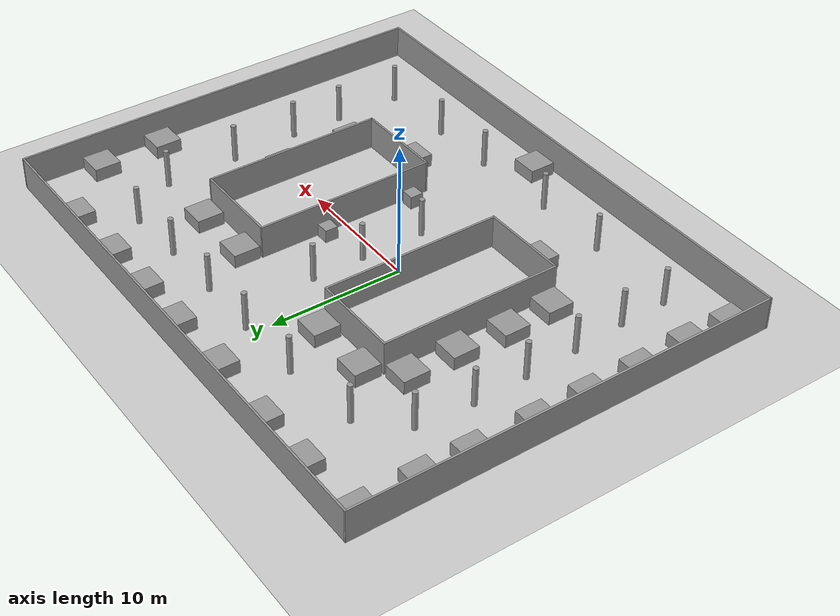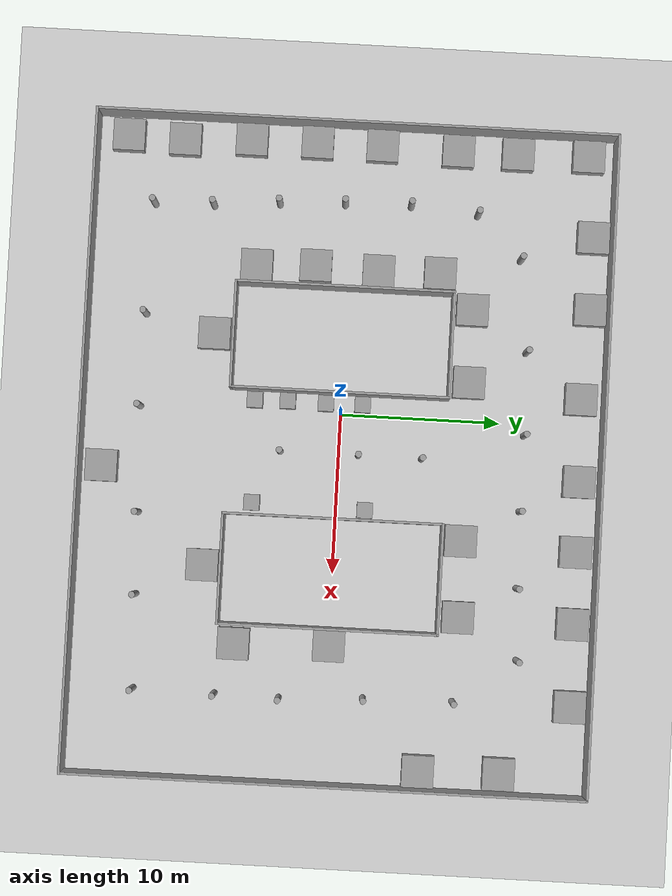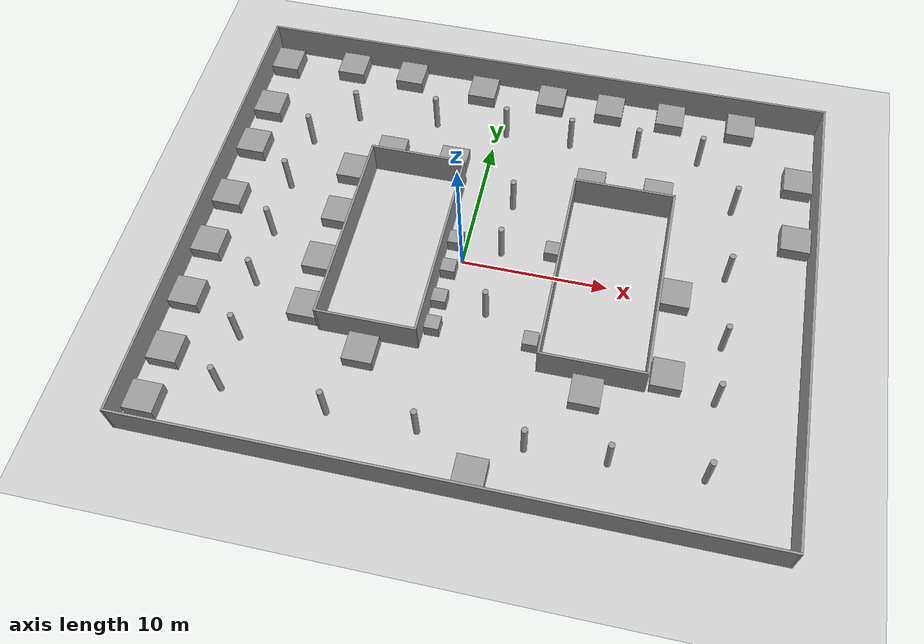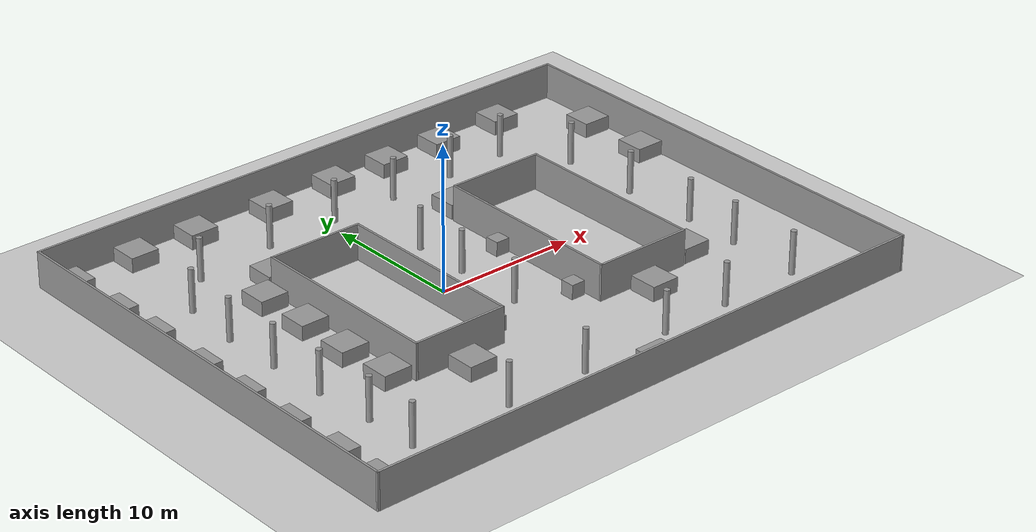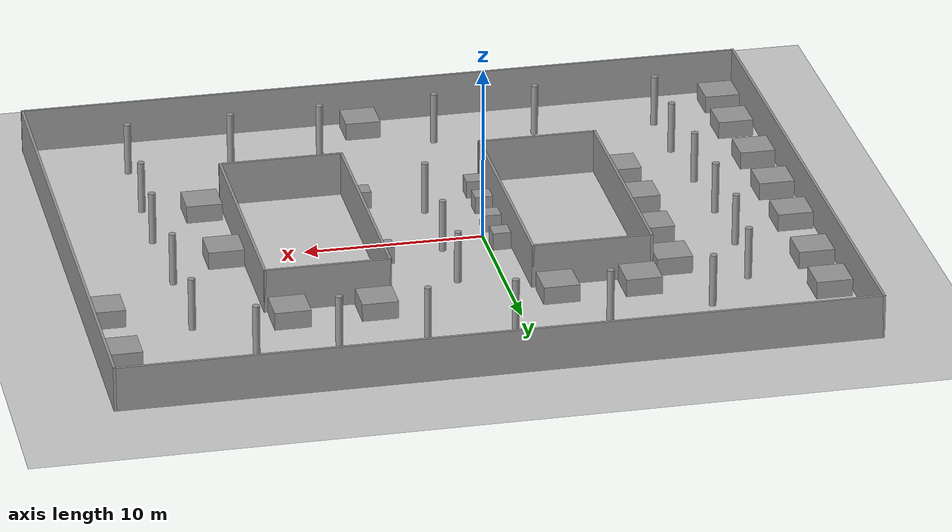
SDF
<sdf version="1.6">
 <world name="default">
  <light name="sun" type="directional">
   <pose>0 0 10 0 -0 0</pose>
   <diffuse>0.8 0.8 0.8 1</diffuse>
   <specular>0.2 0.2 0.2 1</specular>
   <attenuation>
    <range>1000</range>
    <constant>0.9</constant>
    <linear>0.01</linear>
    <quadratic>0.001</quadratic>
   </attenuation>
   <direction>-0.5 0.1 -0.9</direction>
  </light>
  <model name="ground_plane">
   <static>1</static>
   <link name="link">
    <collision name="collision">
     <geometry><plane><normal>0 0 1</normal><size>100 100</size></plane></geometry>
     <surface><friction><ode><mu>100</mu><mu2>50</mu2></ode></friction></surface>
    </collision>
    <visual name="visual">
     <cast_shadows>0</cast_shadows>
     <geometry><plane><normal>0 0 1</normal><size>100 100</size></plane></geometry>
     <material>
      <script><uri>file://media/materials/scripts/gazebo.material</uri><name>Gazebo/Grey</name></script>
     </material>
    </visual>
   </link>
  </model>
  <gravity>0 0 -9.8</gravity>
  <magnetic_field>6e-06 2.3e-05 -4.2e-05</magnetic_field>
  <atmosphere type="adiabatic"/>
  <physics name="default_physics" default="0" type="ode">
   <max_step_size>0.001</max_step_size>
   <real_time_factor>1</real_time_factor>
   <real_time_update_rate>1000</real_time_update_rate>
  </physics>
  <scene><ambient>0.4 0.4 0.4 1</ambient><background>0.7 0.7 0.7 1</background><shadows>1</shadows></scene>
  <spherical_coordinates>
   <surface_model>EARTH_WGS84</surface_model>
   <latitude_deg>0</latitude_deg>
   <longitude_deg>0</longitude_deg>
   <elevation>0</elevation>
   <heading_deg>0</heading_deg>
  </spherical_coordinates>
  <model name="factoy">
   <pose>2.41999 0.117964 0 0 -0 0</pose>
   <link name="Wall_10">
    <collision name="Wall_10_Collision">
     <geometry><box><size>13.75 0.15 2.5</size></box></geometry>
     <pose>0 0 1.25 0 -0 0</pose>
    </collision>
    <visual name="Wall_10_Visual">
     <pose>0 0 1.25 0 -0 0</pose>
     <geometry><box><size>13.75 0.15 2.5</size></box></geometry>
     <material>
      <script><uri>file://media/materials/scripts/gazebo.material</uri><name>Gazebo/Grey</name></script>
      <ambient>1 1 1 1</ambient>
     </material>
     <meta><layer>0</layer></meta>
    </visual>
    <pose>-10.3431 -0.269014 0 0 -0 1.5708</pose>
   </link>
   <link name="Wall_12">
    <collision name="Wall_12_Collision">
     <geometry><box><size>6.75 0.15 2.5</size></box></geometry>
     <pose>0 0 1.25 0 -0 0</pose>
    </collision>
    <visual name="Wall_12_Visual">
     <pose>0 0 1.25 0 -0 0</pose>
     <geometry><box><size>6.75 0.15 2.5</size></box></geometry>
     <material>
      <script><uri>file://media/materials/scripts/gazebo.material</uri><name>Gazebo/Grey</name></script>
      <ambient>1 1 1 1</ambient>
     </material>
     <meta><layer>0</layer></meta>
    </visual>
    <pose>-7.04306 6.53099 0 0 -0 0</pose>
   </link>
   <link name="Wall_13">
    <collision name="Wall_13_Collision">
     <geometry><box><size>13.75 0.15 2.5</size></box></geometry>
     <pose>0 0 1.25 0 -0 0</pose>
    </collision>
    <visual name="Wall_13_Visual">
     <pose>0 0 1.25 0 -0 0</pose>
     <geometry><box><size>13.75 0.15 2.5</size></box></geometry>
     <material>
      <script><uri>file://media/materials/scripts/gazebo.material</uri><name>Gazebo/Grey</name></script>
      <ambient>1 1 1 1</ambient>
     </material>
     <meta><layer>0</layer></meta>
    </visual>
    <pose>-3.74306 -0.269014 0 0 -0 -1.5708</pose>
   </link>
   <link name="Wall_14">
    <collision name="Wall_14_Collision">
     <geometry><box><size>6.75 0.15 2.5</size></box></geometry>
     <pose>0 0 1.25 0 -0 0</pose>
    </collision>
    <visual name="Wall_14_Visual">
     <pose>0 0 1.25 0 -0 0</pose>
     <geometry><box><size>6.75 0.15 2.5</size></box></geometry>
     <material>
      <script><uri>file://media/materials/scripts/gazebo.material</uri><name>Gazebo/Grey</name></script>
      <ambient>1 1 1 1</ambient>
     </material>
     <meta><layer>0</layer></meta>
    </visual>
    <pose>-7.04306 -7.06901 0 0 -0 3.14159</pose>
   </link>
   <link name="Wall_16">
    <collision name="Wall_16_Collision">
     <geometry><box><size>7 0.15 2.5</size></box></geometry>
     <pose>0 0 1.25 0 -0 0</pose>
    </collision>
    <visual name="Wall_16_Visual">
     <pose>0 0 1.25 0 -0 0</pose>
     <geometry><box><size>7 0.15 2.5</size></box></geometry>
     <material>
      <script><uri>file://media/materials/scripts/gazebo.material</uri><name>Gazebo/Grey</name></script>
      <ambient>1 1 1 1</ambient>
     </material>
     <meta><layer>0</layer></meta>
    </visual>
    <pose>7.54301 -7.09389 0 0 -0 3.14159</pose>
   </link>
   <link name="Wall_17">
    <collision name="Wall_17_Collision">
     <geometry><box><size>13.7872 0.15 2.5</size></box></geometry>
     <pose>0 0 1.25 0 -0 0</pose>
    </collision>
    <visual name="Wall_17_Visual">
     <pose>0 0 1.25 0 -0 0</pose>
     <geometry><box><size>13.7872 0.15 2.5</size></box></geometry>
     <material>
      <script><uri>file://media/materials/scripts/gazebo.material</uri><name>Gazebo/Grey</name></script>
      <ambient>1 1 1 1</ambient>
     </material>
     <meta><layer>0</layer></meta>
    </visual>
    <pose>4.11801 -0.248686 0 0 -0 1.5708</pose>
   </link>
   <link name="Wall_18">
    <collision name="Wall_18_Collision">
     <geometry><box><size>7 0.15 2.5</size></box></geometry>
     <pose>0 0 1.25 0 -0 0</pose>
    </collision>
    <visual name="Wall_18_Visual">
     <pose>0 0 1.25 0 -0 0</pose>
     <geometry><box><size>7 0.15 2.5</size></box></geometry>
     <material>
      <script><uri>file://media/materials/scripts/gazebo.material</uri><name>Gazebo/Grey</name></script>
      <ambient>1 1 1 1</ambient>
     </material>
     <meta><layer>0</layer></meta>
    </visual>
    <pose>7.54301 6.56991 0 0 -0 0</pose>
   </link>
   <link name="Wall_2">
    <collision name="Wall_2_Collision">
     <geometry><box><size>41.5 0.15 2.5</size></box></geometry>
     <pose>0 0 1.25 0 -0 0</pose>
    </collision>
    <visual name="Wall_2_Visual">
     <pose>0 0 1.25 0 -0 0</pose>
     <geometry><box><size>41.5 0.15 2.5</size></box></geometry>
     <material>
      <script><uri>file://media/materials/scripts/gazebo.material</uri><name>Gazebo/Grey</name></script>
      <ambient>1 1 1 1</ambient>
     </material>
     <meta><layer>0</layer></meta>
    </visual>
    <pose>-0 16.3 0 0 -0 0</pose>
   </link>
   <link name="Wall_3">
    <collision name="Wall_3_Collision">
     <geometry><box><size>32.751 0.15 2.5</size></box></geometry>
     <pose>0 0 1.25 0 -0 0</pose>
    </collision>
    <visual name="Wall_3_Visual">
     <pose>0 0 1.25 0 -0 0</pose>
     <geometry><box><size>32.751 0.15 2.5</size></box></geometry>
     <material>
      <script><uri>file://media/materials/scripts/gazebo.material</uri><name>Gazebo/Grey</name></script>
      <ambient>1 1 1 1</ambient>
     </material>
     <meta><layer>0</layer></meta>
    </visual>
    <pose>20.675 -0 0 0 -0 -1.5708</pose>
   </link>
   <link name="Wall_4">
    <collision name="Wall_4_Collision">
     <geometry><box><size>41.5 0.15 2.5</size></box></geometry>
     <pose>0 0 1.25 0 -0 0</pose>
    </collision>
    <visual name="Wall_4_Visual">
     <pose>0 0 1.25 0 -0 0</pose>
     <geometry><box><size>41.5 0.15 2.5</size></box></geometry>
     <material>
      <script><uri>file://media/materials/scripts/gazebo.material</uri><name>Gazebo/Grey</name></script>
      <ambient>1 1 1 1</ambient>
     </material>
     <meta><layer>0</layer></meta>
    </visual>
    <pose>-0 -16.3 0 0 -0 3.14159</pose>
   </link>
   <link name="Wall_5">
    <collision name="Wall_5_Collision">
     <geometry><box><size>32.75 0.15 2.5</size></box></geometry>
     <pose>0 0 1.25 0 -0 0</pose>
    </collision>
    <visual name="Wall_5_Visual">
     <pose>0 0 1.25 0 -0 0</pose>
     <geometry><box><size>32.75 0.15 2.5</size></box></geometry>
     <material>
      <script><uri>file://media/materials/scripts/gazebo.material</uri><name>Gazebo/Grey</name></script>
      <ambient>1 1 1 1</ambient>
     </material>
     <meta><layer>0</layer></meta>
    </visual>
    <pose>-20.675 -0 0 0 -0 1.5708</pose>
   </link>
   <link name="Wall_8">
    <collision name="Wall_8_Collision">
     <geometry><box><size>13.7872 0.15 2.5</size></box></geometry>
     <pose>0 0 1.25 0 -0 0</pose>
    </collision>
    <visual name="Wall_8_Visual">
     <pose>0 0 1.25 0 -0 0</pose>
     <geometry><box><size>13.7872 0.15 2.5</size></box></geometry>
     <material>
      <script><uri>file://media/materials/scripts/gazebo.material</uri><name>Gazebo/Grey</name></script>
      <ambient>1 1 1 1</ambient>
     </material>
     <meta><layer>0</layer></meta>
    </visual>
    <pose>10.968 -0.248686 0 0 -0 -1.5708</pose>
   </link>
   <static>1</static>
  </model>
  <model name="box3">
   <link name="link_0">
    <inertial>
     <mass>200</mass>
     <inertia><ixx>83.3333</ixx><ixy>0</ixy><ixz>0</ixz><iyy>83.3333</iyy><iyz>0</iyz><izz>133.333</izz></inertia>
     <pose>0 0 1 0 -0 0</pose>
    </inertial>
    <visual name="visual">
     <geometry><box><size>2 2 1</size></box></geometry>
     <material>
      <lighting>1</lighting>
      <script><uri>file://media/materials/scripts/gazebo.material</uri><name>Gazebo/Grey</name></script>
      <shader type="pixel"><normal_map>__default__</normal_map></shader>
      <ambient>0.3 0.3 0.3 1</ambient>
      <diffuse>0.7 0.7 0.7 1</diffuse>
      <specular>0.01 0.01 0.01 1</specular>
      <emissive>0 0 0 1</emissive>
     </material>
    </visual>
    <collision name="collision">
     <geometry><box><size>2 2 1</size></box></geometry>
     <surface>
      <friction>
       <ode><mu>1</mu><mu2>1</mu2><fdir1>0 0 0</fdir1><slip1>0</slip1><slip2>0</slip2></ode>
       <torsional>
        <coefficient>1</coefficient>
        <patch_radius>0</patch_radius>
        <surface_radius>0</surface_radius>
        <use_patch_radius>1</use_patch_radius>
        <ode><slip>0</slip></ode>
       </torsional>
      </friction>
      <bounce><restitution_coefficient>0</restitution_coefficient><threshold>1e+06</threshold></bounce>
      <contact>
       <collide_without_contact>0</collide_without_contact>
       <collide_without_contact_bitmask>1</collide_without_contact_bitmask>
       <collide_bitmask>1</collide_bitmask>
       <ode>
        <soft_cfm>0</soft_cfm>
        <soft_erp>0.2</soft_erp>
        <kp>1e+13</kp>
        <kd>1</kd>
        <max_vel>0.01</max_vel>
        <min_depth>0</min_depth>
       </ode>
       <bullet>
        <split_impulse>1</split_impulse>
        <split_impulse_penetration_threshold>-0.01</split_impulse_penetration_threshold>
        <soft_cfm>0</soft_cfm>
        <soft_erp>0.2</soft_erp>
        <kp>1e+13</kp>
        <kd>1</kd>
       </bullet>
      </contact>
     </surface>
    </collision>
   </link>
   <static>0</static>
   <pose>-17.0674 1.73296 0.5 0 -0 -0.005346</pose>
  </model>
  <model name="box3_clone">
   <link name="link_0">
    <inertial>
     <mass>200</mass>
     <inertia><ixx>83.3333</ixx><ixy>0</ixy><ixz>0</ixz><iyy>83.3333</iyy><iyz>0</iyz><izz>133.333</izz></inertia>
     <pose>0 0 1 0 -0 0</pose>
    </inertial>
    <visual name="visual">
     <geometry><box><size>2 2 1</size></box></geometry>
     <material>
      <lighting>1</lighting>
      <script><uri>file://media/materials/scripts/gazebo.material</uri><name>Gazebo/Grey</name></script>
      <shader type="pixel"><normal_map>__default__</normal_map></shader>
      <ambient>0.3 0.3 0.3 1</ambient>
      <diffuse>0.7 0.7 0.7 1</diffuse>
      <specular>0.01 0.01 0.01 1</specular>
      <emissive>0 0 0 1</emissive>
     </material>
    </visual>
    <collision name="collision">
     <geometry><box><size>2 2 1</size></box></geometry>
     <surface>
      <friction>
       <ode><mu>1</mu><mu2>1</mu2><fdir1>0 0 0</fdir1><slip1>0</slip1><slip2>0</slip2></ode>
       <torsional>
        <coefficient>1</coefficient>
        <patch_radius>0</patch_radius>
        <surface_radius>0</surface_radius>
        <use_patch_radius>1</use_patch_radius>
        <ode><slip>0</slip></ode>
       </torsional>
      </friction>
      <bounce><restitution_coefficient>0</restitution_coefficient><threshold>1e+06</threshold></bounce>
      <contact>
       <collide_without_contact>0</collide_without_contact>
       <collide_without_contact_bitmask>1</collide_without_contact_bitmask>
       <collide_bitmask>1</collide_bitmask>
       <ode>
        <soft_cfm>0</soft_cfm>
        <soft_erp>0.2</soft_erp>
        <kp>1e+13</kp>
        <kd>1</kd>
        <max_vel>0.01</max_vel>
        <min_depth>0</min_depth>
       </ode>
       <bullet>
        <split_impulse>1</split_impulse>
        <split_impulse_penetration_threshold>-0.01</split_impulse_penetration_threshold>
        <soft_cfm>0</soft_cfm>
        <soft_erp>0.2</soft_erp>
        <kp>1e+13</kp>
        <kd>1</kd>
       </bullet>
      </contact>
     </surface>
    </collision>
   </link>
   <static>0</static>
   <pose>-17.0664 -2.36654 0.499987 -3e-06 0 -0.003809</pose>
  </model>
  <model name="box3_clone_clone">
   <link name="link_0">
    <inertial>
     <mass>200</mass>
     <inertia><ixx>83.3333</ixx><ixy>0</ixy><ixz>0</ixz><iyy>83.3333</iyy><iyz>0</iyz><izz>133.333</izz></inertia>
     <pose>0 0 1 0 -0 0</pose>
    </inertial>
    <visual name="visual">
     <geometry><box><size>2 2 1</size></box></geometry>
     <material>
      <lighting>1</lighting>
      <script><uri>file://media/materials/scripts/gazebo.material</uri><name>Gazebo/Grey</name></script>
      <shader type="pixel"><normal_map>__default__</normal_map></shader>
      <ambient>0.3 0.3 0.3 1</ambient>
      <diffuse>0.7 0.7 0.7 1</diffuse>
      <specular>0.01 0.01 0.01 1</specular>
      <emissive>0 0 0 1</emissive>
     </material>
    </visual>
    <collision name="collision">
     <geometry><box><size>2 2 1</size></box></geometry>
     <surface>
      <friction>
       <ode><mu>1</mu><mu2>1</mu2><fdir1>0 0 0</fdir1><slip1>0</slip1><slip2>0</slip2></ode>
       <torsional>
        <coefficient>1</coefficient>
        <patch_radius>0</patch_radius>
        <surface_radius>0</surface_radius>
        <use_patch_radius>1</use_patch_radius>
        <ode><slip>0</slip></ode>
       </torsional>
      </friction>
      <bounce><restitution_coefficient>0</restitution_coefficient><threshold>1e+06</threshold></bounce>
      <contact>
       <collide_without_contact>0</collide_without_contact>
       <collide_without_contact_bitmask>1</collide_without_contact_bitmask>
       <collide_bitmask>1</collide_bitmask>
       <ode>
        <soft_cfm>0</soft_cfm>
        <soft_erp>0.2</soft_erp>
        <kp>1e+13</kp>
        <kd>1</kd>
        <max_vel>0.01</max_vel>
        <min_depth>0</min_depth>
       </ode>
       <bullet>
        <split_impulse>1</split_impulse>
        <split_impulse_penetration_threshold>-0.01</split_impulse_penetration_threshold>
        <soft_cfm>0</soft_cfm>
        <soft_erp>0.2</soft_erp>
        <kp>1e+13</kp>
        <kd>1</kd>
       </bullet>
      </contact>
     </surface>
    </collision>
   </link>
   <static>0</static>
   <pose>-17.0325 -6.50753 0.49999 -1e-06 0 -0.004666</pose>
  </model>
  <model name="box3_clone_clone_0">
   <link name="link_0">
    <inertial>
     <mass>200</mass>
     <inertia><ixx>83.3333</ixx><ixy>0</ixy><ixz>0</ixz><iyy>83.3333</iyy><iyz>0</iyz><izz>133.333</izz></inertia>
     <pose>0 0 1 0 -0 0</pose>
    </inertial>
    <visual name="visual">
     <geometry><box><size>2 2 1</size></box></geometry>
     <material>
      <lighting>1</lighting>
      <script><uri>file://media/materials/scripts/gazebo.material</uri><name>Gazebo/Grey</name></script>
      <shader type="pixel"><normal_map>__default__</normal_map></shader>
      <ambient>0.3 0.3 0.3 1</ambient>
      <diffuse>0.7 0.7 0.7 1</diffuse>
      <specular>0.01 0.01 0.01 1</specular>
      <emissive>0 0 0 1</emissive>
     </material>
    </visual>
    <collision name="collision">
     <geometry><box><size>2 2 1</size></box></geometry>
     <surface>
      <friction>
       <ode><mu>1</mu><mu2>1</mu2><fdir1>0 0 0</fdir1><slip1>0</slip1><slip2>0</slip2></ode>
       <torsional>
        <coefficient>1</coefficient>
        <patch_radius>0</patch_radius>
        <surface_radius>0</surface_radius>
        <use_patch_radius>1</use_patch_radius>
        <ode><slip>0</slip></ode>
       </torsional>
      </friction>
      <bounce><restitution_coefficient>0</restitution_coefficient><threshold>1e+06</threshold></bounce>
      <contact>
       <collide_without_contact>0</collide_without_contact>
       <collide_without_contact_bitmask>1</collide_without_contact_bitmask>
       <collide_bitmask>1</collide_bitmask>
       <ode>
        <soft_cfm>0</soft_cfm>
        <soft_erp>0.2</soft_erp>
        <kp>1e+13</kp>
        <kd>1</kd>
        <max_vel>0.01</max_vel>
        <min_depth>0</min_depth>
       </ode>
       <bullet>
        <split_impulse>1</split_impulse>
        <split_impulse_penetration_threshold>-0.01</split_impulse_penetration_threshold>
        <soft_cfm>0</soft_cfm>
        <soft_erp>0.2</soft_erp>
        <kp>1e+13</kp>
        <kd>1</kd>
       </bullet>
      </contact>
     </surface>
    </collision>
   </link>
   <static>0</static>
   <pose>-9.12769 -5.78631 0.5 0 -0 0.000104</pose>
  </model>
  <model name="box3_clone_clone_1">
   <link name="link_0">
    <inertial>
     <mass>200</mass>
     <inertia><ixx>83.3333</ixx><ixy>0</ixy><ixz>0</ixz><iyy>83.3333</iyy><iyz>0</iyz><izz>133.333</izz></inertia>
     <pose>0 0 1 0 -0 0</pose>
    </inertial>
    <visual name="visual">
     <geometry><box><size>2 2 1</size></box></geometry>
     <material>
      <lighting>1</lighting>
      <script><uri>file://media/materials/scripts/gazebo.material</uri><name>Gazebo/Grey</name></script>
      <shader type="pixel"><normal_map>__default__</normal_map></shader>
      <ambient>0.3 0.3 0.3 1</ambient>
      <diffuse>0.7 0.7 0.7 1</diffuse>
      <specular>0.01 0.01 0.01 1</specular>
      <emissive>0 0 0 1</emissive>
     </material>
    </visual>
    <collision name="collision">
     <geometry><box><size>2 2 1</size></box></geometry>
     <surface>
      <friction>
       <ode><mu>1</mu><mu2>1</mu2><fdir1>0 0 0</fdir1><slip1>0</slip1><slip2>0</slip2></ode>
       <torsional>
        <coefficient>1</coefficient>
        <patch_radius>0</patch_radius>
        <surface_radius>0</surface_radius>
        <use_patch_radius>1</use_patch_radius>
        <ode><slip>0</slip></ode>
       </torsional>
      </friction>
      <bounce><restitution_coefficient>0</restitution_coefficient><threshold>1e+06</threshold></bounce>
      <contact>
       <collide_without_contact>0</collide_without_contact>
       <collide_without_contact_bitmask>1</collide_without_contact_bitmask>
       <collide_bitmask>1</collide_bitmask>
       <ode>
        <soft_cfm>0</soft_cfm>
        <soft_erp>0.2</soft_erp>
        <kp>1e+13</kp>
        <kd>1</kd>
        <max_vel>0.01</max_vel>
        <min_depth>0</min_depth>
       </ode>
       <bullet>
        <split_impulse>1</split_impulse>
        <split_impulse_penetration_threshold>-0.01</split_impulse_penetration_threshold>
        <soft_cfm>0</soft_cfm>
        <soft_erp>0.2</soft_erp>
        <kp>1e+13</kp>
        <kd>1</kd>
       </bullet>
      </contact>
     </surface>
    </collision>
   </link>
   <static>0</static>
   <pose>-9.30672 -2.07253 0.5 0 -0 0.000104</pose>
  </model>
  <model name="box3_clone_clone_2">
   <link name="link_0">
    <inertial>
     <mass>200</mass>
     <inertia><ixx>83.3333</ixx><ixy>0</ixy><ixz>0</ixz><iyy>83.3333</iyy><iyz>0</iyz><izz>133.333</izz></inertia>
     <pose>0 0 1 0 -0 0</pose>
    </inertial>
    <visual name="visual">
     <geometry><box><size>2 2 1</size></box></geometry>
     <material>
      <lighting>1</lighting>
      <script><uri>file://media/materials/scripts/gazebo.material</uri><name>Gazebo/Grey</name></script>
      <shader type="pixel"><normal_map>__default__</normal_map></shader>
      <ambient>0.3 0.3 0.3 1</ambient>
      <diffuse>0.7 0.7 0.7 1</diffuse>
      <specular>0.01 0.01 0.01 1</specular>
      <emissive>0 0 0 1</emissive>
     </material>
    </visual>
    <collision name="collision">
     <geometry><box><size>2 2 1</size></box></geometry>
     <surface>
      <friction>
       <ode><mu>1</mu><mu2>1</mu2><fdir1>0 0 0</fdir1><slip1>0</slip1><slip2>0</slip2></ode>
       <torsional>
        <coefficient>1</coefficient>
        <patch_radius>0</patch_radius>
        <surface_radius>0</surface_radius>
        <use_patch_radius>1</use_patch_radius>
        <ode><slip>0</slip></ode>
       </torsional>
      </friction>
      <bounce><restitution_coefficient>0</restitution_coefficient><threshold>1e+06</threshold></bounce>
      <contact>
       <collide_without_contact>0</collide_without_contact>
       <collide_without_contact_bitmask>1</collide_without_contact_bitmask>
       <collide_bitmask>1</collide_bitmask>
       <ode>
        <soft_cfm>0</soft_cfm>
        <soft_erp>0.2</soft_erp>
        <kp>1e+13</kp>
        <kd>1</kd>
        <max_vel>0.01</max_vel>
        <min_depth>0</min_depth>
       </ode>
       <bullet>
        <split_impulse>1</split_impulse>
        <split_impulse_penetration_threshold>-0.01</split_impulse_penetration_threshold>
        <soft_cfm>0</soft_cfm>
        <soft_erp>0.2</soft_erp>
        <kp>1e+13</kp>
        <kd>1</kd>
       </bullet>
      </contact>
     </surface>
    </collision>
   </link>
   <static>0</static>
   <pose>-9.1685 1.88848 0.5 0 -0 0.000104</pose>
  </model>
  <model name="box3_clone_0">
   <link name="link_0">
    <inertial>
     <mass>200</mass>
     <inertia><ixx>83.3333</ixx><ixy>0</ixy><ixz>0</ixz><iyy>83.3333</iyy><iyz>0</iyz><izz>133.333</izz></inertia>
     <pose>0 0 1 0 -0 0</pose>
    </inertial>
    <visual name="visual">
     <geometry><box><size>2 2 1</size></box></geometry>
     <material>
      <lighting>1</lighting>
      <script><uri>file://media/materials/scripts/gazebo.material</uri><name>Gazebo/Grey</name></script>
      <shader type="pixel"><normal_map>__default__</normal_map></shader>
      <ambient>0.3 0.3 0.3 1</ambient>
      <diffuse>0.7 0.7 0.7 1</diffuse>
      <specular>0.01 0.01 0.01 1</specular>
      <emissive>0 0 0 1</emissive>
     </material>
    </visual>
    <collision name="collision">
     <geometry><box><size>2 2 1</size></box></geometry>
     <surface>
      <friction>
       <ode><mu>1</mu><mu2>1</mu2><fdir1>0 0 0</fdir1><slip1>0</slip1><slip2>0</slip2></ode>
       <torsional>
        <coefficient>1</coefficient>
        <patch_radius>0</patch_radius>
        <surface_radius>0</surface_radius>
        <use_patch_radius>1</use_patch_radius>
        <ode><slip>0</slip></ode>
       </torsional>
      </friction>
      <bounce><restitution_coefficient>0</restitution_coefficient><threshold>1e+06</threshold></bounce>
      <contact>
       <collide_without_contact>0</collide_without_contact>
       <collide_without_contact_bitmask>1</collide_without_contact_bitmask>
       <collide_bitmask>1</collide_bitmask>
       <ode>
        <soft_cfm>0</soft_cfm>
        <soft_erp>0.2</soft_erp>
        <kp>1e+13</kp>
        <kd>1</kd>
        <max_vel>0.01</max_vel>
        <min_depth>0</min_depth>
       </ode>
       <bullet>
        <split_impulse>1</split_impulse>
        <split_impulse_penetration_threshold>-0.01</split_impulse_penetration_threshold>
        <soft_cfm>0</soft_cfm>
        <soft_erp>0.2</soft_erp>
        <kp>1e+13</kp>
        <kd>1</kd>
       </bullet>
      </contact>
     </surface>
    </collision>
   </link>
   <static>0</static>
   <pose>-16.9918 6.52351 0.499986 -1e-06 3e-06 -0.005185</pose>
  </model>
  <model name="box3_clone_1">
   <link name="link_0">
    <inertial>
     <mass>200</mass>
     <inertia><ixx>83.3333</ixx><ixy>0</ixy><ixz>0</ixz><iyy>83.3333</iyy><iyz>0</iyz><izz>133.333</izz></inertia>
     <pose>0 0 1 0 -0 0</pose>
    </inertial>
    <visual name="visual">
     <geometry><box><size>2 2 1</size></box></geometry>
     <material>
      <lighting>1</lighting>
      <script><uri>file://media/materials/scripts/gazebo.material</uri><name>Gazebo/Grey</name></script>
      <shader type="pixel"><normal_map>__default__</normal_map></shader>
      <ambient>0.3 0.3 0.3 1</ambient>
      <diffuse>0.7 0.7 0.7 1</diffuse>
      <specular>0.01 0.01 0.01 1</specular>
      <emissive>0 0 0 1</emissive>
     </material>
    </visual>
    <collision name="collision">
     <geometry><box><size>2 2 1</size></box></geometry>
     <surface>
      <friction>
       <ode><mu>1</mu><mu2>1</mu2><fdir1>0 0 0</fdir1><slip1>0</slip1><slip2>0</slip2></ode>
       <torsional>
        <coefficient>1</coefficient>
        <patch_radius>0</patch_radius>
        <surface_radius>0</surface_radius>
        <use_patch_radius>1</use_patch_radius>
        <ode><slip>0</slip></ode>
       </torsional>
      </friction>
      <bounce><restitution_coefficient>0</restitution_coefficient><threshold>1e+06</threshold></bounce>
      <contact>
       <collide_without_contact>0</collide_without_contact>
       <collide_without_contact_bitmask>1</collide_without_contact_bitmask>
       <collide_bitmask>1</collide_bitmask>
       <ode>
        <soft_cfm>0</soft_cfm>
        <soft_erp>0.2</soft_erp>
        <kp>1e+13</kp>
        <kd>1</kd>
        <max_vel>0.01</max_vel>
        <min_depth>0</min_depth>
       </ode>
       <bullet>
        <split_impulse>1</split_impulse>
        <split_impulse_penetration_threshold>-0.01</split_impulse_penetration_threshold>
        <soft_cfm>0</soft_cfm>
        <soft_erp>0.2</soft_erp>
        <kp>1e+13</kp>
        <kd>1</kd>
       </bullet>
      </contact>
     </surface>
    </collision>
   </link>
   <static>0</static>
   <pose>-16.9852 10.2879 0.5 0 -0 0.000104</pose>
  </model>
  <model name="box3_clone_2">
   <link name="link_0">
    <inertial>
     <mass>200</mass>
     <inertia><ixx>83.3333</ixx><ixy>0</ixy><ixz>0</ixz><iyy>83.3333</iyy><iyz>0</iyz><izz>133.333</izz></inertia>
     <pose>0 0 1 0 -0 0</pose>
    </inertial>
    <visual name="visual">
     <geometry><box><size>2 2 1</size></box></geometry>
     <material>
      <lighting>1</lighting>
      <script><uri>file://media/materials/scripts/gazebo.material</uri><name>Gazebo/Grey</name></script>
      <shader type="pixel"><normal_map>__default__</normal_map></shader>
      <ambient>0.3 0.3 0.3 1</ambient>
      <diffuse>0.7 0.7 0.7 1</diffuse>
      <specular>0.01 0.01 0.01 1</specular>
      <emissive>0 0 0 1</emissive>
     </material>
    </visual>
    <collision name="collision">
     <geometry><box><size>2 2 1</size></box></geometry>
     <surface>
      <friction>
       <ode><mu>1</mu><mu2>1</mu2><fdir1>0 0 0</fdir1><slip1>0</slip1><slip2>0</slip2></ode>
       <torsional>
        <coefficient>1</coefficient>
        <patch_radius>0</patch_radius>
        <surface_radius>0</surface_radius>
        <use_patch_radius>1</use_patch_radius>
        <ode><slip>0</slip></ode>
       </torsional>
      </friction>
      <bounce><restitution_coefficient>0</restitution_coefficient><threshold>1e+06</threshold></bounce>
      <contact>
       <collide_without_contact>0</collide_without_contact>
       <collide_without_contact_bitmask>1</collide_without_contact_bitmask>
       <collide_bitmask>1</collide_bitmask>
       <ode>
        <soft_cfm>0</soft_cfm>
        <soft_erp>0.2</soft_erp>
        <kp>1e+13</kp>
        <kd>1</kd>
        <max_vel>0.01</max_vel>
        <min_depth>0</min_depth>
       </ode>
       <bullet>
        <split_impulse>1</split_impulse>
        <split_impulse_penetration_threshold>-0.01</split_impulse_penetration_threshold>
        <soft_cfm>0</soft_cfm>
        <soft_erp>0.2</soft_erp>
        <kp>1e+13</kp>
        <kd>1</kd>
       </bullet>
      </contact>
     </surface>
    </collision>
   </link>
   <static>0</static>
   <pose>-17.0624 14.7411 0.5 0 -0 0.000104</pose>
  </model>
  <model name="box3_clone_3">
   <link name="link_0">
    <inertial>
     <mass>200</mass>
     <inertia><ixx>83.3333</ixx><ixy>0</ixy><ixz>0</ixz><iyy>83.3333</iyy><iyz>0</iyz><izz>133.333</izz></inertia>
     <pose>0 0 1 0 -0 0</pose>
    </inertial>
    <visual name="visual">
     <geometry><box><size>2 2 1</size></box></geometry>
     <material>
      <lighting>1</lighting>
      <script><uri>file://media/materials/scripts/gazebo.material</uri><name>Gazebo/Grey</name></script>
      <shader type="pixel"><normal_map>__default__</normal_map></shader>
      <ambient>0.3 0.3 0.3 1</ambient>
      <diffuse>0.7 0.7 0.7 1</diffuse>
      <specular>0.01 0.01 0.01 1</specular>
      <emissive>0 0 0 1</emissive>
     </material>
    </visual>
    <collision name="collision">
     <geometry><box><size>2 2 1</size></box></geometry>
     <surface>
      <friction>
       <ode><mu>1</mu><mu2>1</mu2><fdir1>0 0 0</fdir1><slip1>0</slip1><slip2>0</slip2></ode>
       <torsional>
        <coefficient>1</coefficient>
        <patch_radius>0</patch_radius>
        <surface_radius>0</surface_radius>
        <use_patch_radius>1</use_patch_radius>
        <ode><slip>0</slip></ode>
       </torsional>
      </friction>
      <bounce><restitution_coefficient>0</restitution_coefficient><threshold>1e+06</threshold></bounce>
      <contact>
       <collide_without_contact>0</collide_without_contact>
       <collide_without_contact_bitmask>1</collide_without_contact_bitmask>
       <collide_bitmask>1</collide_bitmask>
       <ode>
        <soft_cfm>0</soft_cfm>
        <soft_erp>0.2</soft_erp>
        <kp>1e+13</kp>
        <kd>1</kd>
        <max_vel>0.01</max_vel>
        <min_depth>0</min_depth>
       </ode>
       <bullet>
        <split_impulse>1</split_impulse>
        <split_impulse_penetration_threshold>-0.01</split_impulse_penetration_threshold>
        <soft_cfm>0</soft_cfm>
        <soft_erp>0.2</soft_erp>
        <kp>1e+13</kp>
        <kd>1</kd>
       </bullet>
      </contact>
     </surface>
    </collision>
   </link>
   <static>0</static>
   <pose>-9.22346 5.76728 0.5 0 -0 0.000104</pose>
  </model>
  <model name="box3_clone_4">
   <link name="link_0">
    <inertial>
     <mass>200</mass>
     <inertia><ixx>83.3333</ixx><ixy>0</ixy><ixz>0</ixz><iyy>83.3333</iyy><iyz>0</iyz><izz>133.333</izz></inertia>
     <pose>0 0 1 0 -0 0</pose>
    </inertial>
    <visual name="visual">
     <geometry><box><size>2 2 1</size></box></geometry>
     <material>
      <lighting>1</lighting>
      <script><uri>file://media/materials/scripts/gazebo.material</uri><name>Gazebo/Grey</name></script>
      <shader type="pixel"><normal_map>__default__</normal_map></shader>
      <ambient>0.3 0.3 0.3 1</ambient>
      <diffuse>0.7 0.7 0.7 1</diffuse>
      <specular>0.01 0.01 0.01 1</specular>
      <emissive>0 0 0 1</emissive>
     </material>
    </visual>
    <collision name="collision">
     <geometry><box><size>2 2 1</size></box></geometry>
     <surface>
      <friction>
       <ode><mu>1</mu><mu2>1</mu2><fdir1>0 0 0</fdir1><slip1>0</slip1><slip2>0</slip2></ode>
       <torsional>
        <coefficient>1</coefficient>
        <patch_radius>0</patch_radius>
        <surface_radius>0</surface_radius>
        <use_patch_radius>1</use_patch_radius>
        <ode><slip>0</slip></ode>
       </torsional>
      </friction>
      <bounce><restitution_coefficient>0</restitution_coefficient><threshold>1e+06</threshold></bounce>
      <contact>
       <collide_without_contact>0</collide_without_contact>
       <collide_without_contact_bitmask>1</collide_without_contact_bitmask>
       <collide_bitmask>1</collide_bitmask>
       <ode>
        <soft_cfm>0</soft_cfm>
        <soft_erp>0.2</soft_erp>
        <kp>1e+13</kp>
        <kd>1</kd>
        <max_vel>0.01</max_vel>
        <min_depth>0</min_depth>
       </ode>
       <bullet>
        <split_impulse>1</split_impulse>
        <split_impulse_penetration_threshold>-0.01</split_impulse_penetration_threshold>
        <soft_cfm>0</soft_cfm>
        <soft_erp>0.2</soft_erp>
        <kp>1e+13</kp>
        <kd>1</kd>
       </bullet>
      </contact>
     </surface>
    </collision>
   </link>
   <static>0</static>
   <pose>-11.9721 15.2785 0.5 0 -0 0.000104</pose>
  </model>
  <model name="box3_clone_5">
   <link name="link_0">
    <inertial>
     <mass>200</mass>
     <inertia><ixx>83.3333</ixx><ixy>0</ixy><ixz>0</ixz><iyy>83.3333</iyy><iyz>0</iyz><izz>133.333</izz></inertia>
     <pose>0 0 1 0 -0 0</pose>
    </inertial>
    <visual name="visual">
     <geometry><box><size>2 2 1</size></box></geometry>
     <material>
      <lighting>1</lighting>
      <script><uri>file://media/materials/scripts/gazebo.material</uri><name>Gazebo/Grey</name></script>
      <shader type="pixel"><normal_map>__default__</normal_map></shader>
      <ambient>0.3 0.3 0.3 1</ambient>
      <diffuse>0.7 0.7 0.7 1</diffuse>
      <specular>0.01 0.01 0.01 1</specular>
      <emissive>0 0 0 1</emissive>
     </material>
    </visual>
    <collision name="collision">
     <geometry><box><size>2 2 1</size></box></geometry>
     <surface>
      <friction>
       <ode><mu>1</mu><mu2>1</mu2><fdir1>0 0 0</fdir1><slip1>0</slip1><slip2>0</slip2></ode>
       <torsional>
        <coefficient>1</coefficient>
        <patch_radius>0</patch_radius>
        <surface_radius>0</surface_radius>
        <use_patch_radius>1</use_patch_radius>
        <ode><slip>0</slip></ode>
       </torsional>
      </friction>
      <bounce><restitution_coefficient>0</restitution_coefficient><threshold>1e+06</threshold></bounce>
      <contact>
       <collide_without_contact>0</collide_without_contact>
       <collide_without_contact_bitmask>1</collide_without_contact_bitmask>
       <collide_bitmask>1</collide_bitmask>
       <ode>
        <soft_cfm>0</soft_cfm>
        <soft_erp>0.2</soft_erp>
        <kp>1e+13</kp>
        <kd>1</kd>
        <max_vel>0.01</max_vel>
        <min_depth>0</min_depth>
       </ode>
       <bullet>
        <split_impulse>1</split_impulse>
        <split_impulse_penetration_threshold>-0.01</split_impulse_penetration_threshold>
        <soft_cfm>0</soft_cfm>
        <soft_erp>0.2</soft_erp>
        <kp>1e+13</kp>
        <kd>1</kd>
       </bullet>
      </contact>
     </surface>
    </collision>
   </link>
   <static>0</static>
   <pose>-7.41157 15.2979 0.5 0 -0 0.000104</pose>
  </model>
  <model name="box3_clone_6">
   <link name="link_0">
    <inertial>
     <mass>200</mass>
     <inertia><ixx>83.3333</ixx><ixy>0</ixy><ixz>0</ixz><iyy>83.3333</iyy><iyz>0</iyz><izz>133.333</izz></inertia>
     <pose>0 0 1 0 -0 0</pose>
    </inertial>
    <visual name="visual">
     <geometry><box><size>2 2 1</size></box></geometry>
     <material>
      <lighting>1</lighting>
      <script><uri>file://media/materials/scripts/gazebo.material</uri><name>Gazebo/Grey</name></script>
      <shader type="pixel"><normal_map>__default__</normal_map></shader>
      <ambient>0.3 0.3 0.3 1</ambient>
      <diffuse>0.7 0.7 0.7 1</diffuse>
      <specular>0.01 0.01 0.01 1</specular>
      <emissive>0 0 0 1</emissive>
     </material>
    </visual>
    <collision name="collision">
     <geometry><box><size>2 2 1</size></box></geometry>
     <surface>
      <friction>
       <ode><mu>1</mu><mu2>1</mu2><fdir1>0 0 0</fdir1><slip1>0</slip1><slip2>0</slip2></ode>
       <torsional>
        <coefficient>1</coefficient>
        <patch_radius>0</patch_radius>
        <surface_radius>0</surface_radius>
        <use_patch_radius>1</use_patch_radius>
        <ode><slip>0</slip></ode>
       </torsional>
      </friction>
      <bounce><restitution_coefficient>0</restitution_coefficient><threshold>1e+06</threshold></bounce>
      <contact>
       <collide_without_contact>0</collide_without_contact>
       <collide_without_contact_bitmask>1</collide_without_contact_bitmask>
       <collide_bitmask>1</collide_bitmask>
       <ode>
        <soft_cfm>0</soft_cfm>
        <soft_erp>0.2</soft_erp>
        <kp>1e+13</kp>
        <kd>1</kd>
        <max_vel>0.01</max_vel>
        <min_depth>0</min_depth>
       </ode>
       <bullet>
        <split_impulse>1</split_impulse>
        <split_impulse_penetration_threshold>-0.01</split_impulse_penetration_threshold>
        <soft_cfm>0</soft_cfm>
        <soft_erp>0.2</soft_erp>
        <kp>1e+13</kp>
        <kd>1</kd>
       </bullet>
      </contact>
     </surface>
    </collision>
   </link>
   <static>0</static>
   <pose>-7.01543 7.91101 0.5 0 -0 0.000104</pose>
  </model>
  <model name="box3_clone_7">
   <link name="link_0">
    <inertial>
     <mass>200</mass>
     <inertia><ixx>83.3333</ixx><ixy>0</ixy><ixz>0</ixz><iyy>83.3333</iyy><iyz>0</iyz><izz>133.333</izz></inertia>
     <pose>0 0 1 0 -0 0</pose>
    </inertial>
    <visual name="visual">
     <geometry><box><size>2 2 1</size></box></geometry>
     <material>
      <lighting>1</lighting>
      <script><uri>file://media/materials/scripts/gazebo.material</uri><name>Gazebo/Grey</name></script>
      <shader type="pixel"><normal_map>__default__</normal_map></shader>
      <ambient>0.3 0.3 0.3 1</ambient>
      <diffuse>0.7 0.7 0.7 1</diffuse>
      <specular>0.01 0.01 0.01 1</specular>
      <emissive>0 0 0 1</emissive>
     </material>
    </visual>
    <collision name="collision">
     <geometry><box><size>2 2 1</size></box></geometry>
     <surface>
      <friction>
       <ode><mu>1</mu><mu2>1</mu2><fdir1>0 0 0</fdir1><slip1>0</slip1><slip2>0</slip2></ode>
       <torsional>
        <coefficient>1</coefficient>
        <patch_radius>0</patch_radius>
        <surface_radius>0</surface_radius>
        <use_patch_radius>1</use_patch_radius>
        <ode><slip>0</slip></ode>
       </torsional>
      </friction>
      <bounce><restitution_coefficient>0</restitution_coefficient><threshold>1e+06</threshold></bounce>
      <contact>
       <collide_without_contact>0</collide_without_contact>
       <collide_without_contact_bitmask>1</collide_without_contact_bitmask>
       <collide_bitmask>1</collide_bitmask>
       <ode>
        <soft_cfm>0</soft_cfm>
        <soft_erp>0.2</soft_erp>
        <kp>1e+13</kp>
        <kd>1</kd>
        <max_vel>0.01</max_vel>
        <min_depth>0</min_depth>
       </ode>
       <bullet>
        <split_impulse>1</split_impulse>
        <split_impulse_penetration_threshold>-0.01</split_impulse_penetration_threshold>
        <soft_cfm>0</soft_cfm>
        <soft_erp>0.2</soft_erp>
        <kp>1e+13</kp>
        <kd>1</kd>
       </bullet>
      </contact>
     </surface>
    </collision>
   </link>
   <static>0</static>
   <pose>-2.44061 7.92404 0.5 0 -0 0.000104</pose>
  </model>
  <model name="box3_clone_8">
   <link name="link_0">
    <inertial>
     <mass>200</mass>
     <inertia><ixx>83.3333</ixx><ixy>0</ixy><ixz>0</ixz><iyy>83.3333</iyy><iyz>0</iyz><izz>133.333</izz></inertia>
     <pose>0 0 1 0 -0 0</pose>
    </inertial>
    <visual name="visual">
     <geometry><box><size>2 2 1</size></box></geometry>
     <material>
      <lighting>1</lighting>
      <script><uri>file://media/materials/scripts/gazebo.material</uri><name>Gazebo/Grey</name></script>
      <shader type="pixel"><normal_map>__default__</normal_map></shader>
      <ambient>0.3 0.3 0.3 1</ambient>
      <diffuse>0.7 0.7 0.7 1</diffuse>
      <specular>0.01 0.01 0.01 1</specular>
      <emissive>0 0 0 1</emissive>
     </material>
    </visual>
    <collision name="collision">
     <geometry><box><size>2 2 1</size></box></geometry>
     <surface>
      <friction>
       <ode><mu>1</mu><mu2>1</mu2><fdir1>0 0 0</fdir1><slip1>0</slip1><slip2>0</slip2></ode>
       <torsional>
        <coefficient>1</coefficient>
        <patch_radius>0</patch_radius>
        <surface_radius>0</surface_radius>
        <use_patch_radius>1</use_patch_radius>
        <ode><slip>0</slip></ode>
       </torsional>
      </friction>
      <bounce><restitution_coefficient>0</restitution_coefficient><threshold>1e+06</threshold></bounce>
      <contact>
       <collide_without_contact>0</collide_without_contact>
       <collide_without_contact_bitmask>1</collide_without_contact_bitmask>
       <collide_bitmask>1</collide_bitmask>
       <ode>
        <soft_cfm>0</soft_cfm>
        <soft_erp>0.2</soft_erp>
        <kp>1e+13</kp>
        <kd>1</kd>
        <max_vel>0.01</max_vel>
        <min_depth>0</min_depth>
       </ode>
       <bullet>
        <split_impulse>1</split_impulse>
        <split_impulse_penetration_threshold>-0.01</split_impulse_penetration_threshold>
        <soft_cfm>0</soft_cfm>
        <soft_erp>0.2</soft_erp>
        <kp>1e+13</kp>
        <kd>1</kd>
       </bullet>
      </contact>
     </surface>
    </collision>
   </link>
   <static>0</static>
   <pose>7.50618 7.90798 0.5 0 0 -0.000118</pose>
  </model>
  <model name="box3_clone_9">
   <link name="link_0">
    <inertial>
     <mass>200</mass>
     <inertia><ixx>83.3333</ixx><ixy>0</ixy><ixz>0</ixz><iyy>83.3333</iyy><iyz>0</iyz><izz>133.333</izz></inertia>
     <pose>0 0 1 0 -0 0</pose>
    </inertial>
    <visual name="visual">
     <geometry><box><size>2 2 1</size></box></geometry>
     <material>
      <lighting>1</lighting>
      <script><uri>file://media/materials/scripts/gazebo.material</uri><name>Gazebo/Grey</name></script>
      <shader type="pixel"><normal_map>__default__</normal_map></shader>
      <ambient>0.3 0.3 0.3 1</ambient>
      <diffuse>0.7 0.7 0.7 1</diffuse>
      <specular>0.01 0.01 0.01 1</specular>
      <emissive>0 0 0 1</emissive>
     </material>
    </visual>
    <collision name="collision">
     <geometry><box><size>2 2 1</size></box></geometry>
     <surface>
      <friction>
       <ode><mu>1</mu><mu2>1</mu2><fdir1>0 0 0</fdir1><slip1>0</slip1><slip2>0</slip2></ode>
       <torsional>
        <coefficient>1</coefficient>
        <patch_radius>0</patch_radius>
        <surface_radius>0</surface_radius>
        <use_patch_radius>1</use_patch_radius>
        <ode><slip>0</slip></ode>
       </torsional>
      </friction>
      <bounce><restitution_coefficient>0</restitution_coefficient><threshold>1e+06</threshold></bounce>
      <contact>
       <collide_without_contact>0</collide_without_contact>
       <collide_without_contact_bitmask>1</collide_without_contact_bitmask>
       <collide_bitmask>1</collide_bitmask>
       <ode>
        <soft_cfm>0</soft_cfm>
        <soft_erp>0.2</soft_erp>
        <kp>1e+13</kp>
        <kd>1</kd>
        <max_vel>0.01</max_vel>
        <min_depth>0</min_depth>
       </ode>
       <bullet>
        <split_impulse>1</split_impulse>
        <split_impulse_penetration_threshold>-0.01</split_impulse_penetration_threshold>
        <soft_cfm>0</soft_cfm>
        <soft_erp>0.2</soft_erp>
        <kp>1e+13</kp>
        <kd>1</kd>
       </bullet>
      </contact>
     </surface>
    </collision>
   </link>
   <static>0</static>
   <pose>12.2831 7.97717 0.5 0 -0 0.000104</pose>
  </model>
  <model name="box3_clone_10">
   <link name="link_0">
    <inertial>
     <mass>200</mass>
     <inertia><ixx>83.3333</ixx><ixy>0</ixy><ixz>0</ixz><iyy>83.3333</iyy><iyz>0</iyz><izz>133.333</izz></inertia>
     <pose>0 0 1 0 -0 0</pose>
    </inertial>
    <visual name="visual">
     <geometry><box><size>2 2 1</size></box></geometry>
     <material>
      <lighting>1</lighting>
      <script><uri>file://media/materials/scripts/gazebo.material</uri><name>Gazebo/Grey</name></script>
      <shader type="pixel"><normal_map>__default__</normal_map></shader>
      <ambient>0.3 0.3 0.3 1</ambient>
      <diffuse>0.7 0.7 0.7 1</diffuse>
      <specular>0.01 0.01 0.01 1</specular>
      <emissive>0 0 0 1</emissive>
     </material>
    </visual>
    <collision name="collision">
     <geometry><box><size>2 2 1</size></box></geometry>
     <surface>
      <friction>
       <ode><mu>1</mu><mu2>1</mu2><fdir1>0 0 0</fdir1><slip1>0</slip1><slip2>0</slip2></ode>
       <torsional>
        <coefficient>1</coefficient>
        <patch_radius>0</patch_radius>
        <surface_radius>0</surface_radius>
        <use_patch_radius>1</use_patch_radius>
        <ode><slip>0</slip></ode>
       </torsional>
      </friction>
      <bounce><restitution_coefficient>0</restitution_coefficient><threshold>1e+06</threshold></bounce>
      <contact>
       <collide_without_contact>0</collide_without_contact>
       <collide_without_contact_bitmask>1</collide_without_contact_bitmask>
       <collide_bitmask>1</collide_bitmask>
       <ode>
        <soft_cfm>0</soft_cfm>
        <soft_erp>0.2</soft_erp>
        <kp>1e+13</kp>
        <kd>1</kd>
        <max_vel>0.01</max_vel>
        <min_depth>0</min_depth>
       </ode>
       <bullet>
        <split_impulse>1</split_impulse>
        <split_impulse_penetration_threshold>-0.01</split_impulse_penetration_threshold>
        <soft_cfm>0</soft_cfm>
        <soft_erp>0.2</soft_erp>
        <kp>1e+13</kp>
        <kd>1</kd>
       </bullet>
      </contact>
     </surface>
    </collision>
   </link>
   <static>0</static>
   <pose>7.82772 15.1347 0.5 0 -0 0.000104</pose>
  </model>
  <model name="box3_clone_11">
   <link name="link_0">
    <inertial>
     <mass>200</mass>
     <inertia><ixx>83.3333</ixx><ixy>0</ixy><ixz>0</ixz><iyy>83.3333</iyy><iyz>0</iyz><izz>133.333</izz></inertia>
     <pose>0 0 1 0 -0 0</pose>
    </inertial>
    <visual name="visual">
     <geometry><box><size>2 2 1</size></box></geometry>
     <material>
      <lighting>1</lighting>
      <script><uri>file://media/materials/scripts/gazebo.material</uri><name>Gazebo/Grey</name></script>
      <shader type="pixel"><normal_map>__default__</normal_map></shader>
      <ambient>0.3 0.3 0.3 1</ambient>
      <diffuse>0.7 0.7 0.7 1</diffuse>
      <specular>0.01 0.01 0.01 1</specular>
      <emissive>0 0 0 1</emissive>
     </material>
    </visual>
    <collision name="collision">
     <geometry><box><size>2 2 1</size></box></geometry>
     <surface>
      <friction>
       <ode><mu>1</mu><mu2>1</mu2><fdir1>0 0 0</fdir1><slip1>0</slip1><slip2>0</slip2></ode>
       <torsional>
        <coefficient>1</coefficient>
        <patch_radius>0</patch_radius>
        <surface_radius>0</surface_radius>
        <use_patch_radius>1</use_patch_radius>
        <ode><slip>0</slip></ode>
       </torsional>
      </friction>
      <bounce><restitution_coefficient>0</restitution_coefficient><threshold>1e+06</threshold></bounce>
      <contact>
       <collide_without_contact>0</collide_without_contact>
       <collide_without_contact_bitmask>1</collide_without_contact_bitmask>
       <collide_bitmask>1</collide_bitmask>
       <ode>
        <soft_cfm>0</soft_cfm>
        <soft_erp>0.2</soft_erp>
        <kp>1e+13</kp>
        <kd>1</kd>
        <max_vel>0.01</max_vel>
        <min_depth>0</min_depth>
       </ode>
       <bullet>
        <split_impulse>1</split_impulse>
        <split_impulse_penetration_threshold>-0.01</split_impulse_penetration_threshold>
        <soft_cfm>0</soft_cfm>
        <soft_erp>0.2</soft_erp>
        <kp>1e+13</kp>
        <kd>1</kd>
       </bullet>
      </contact>
     </surface>
    </collision>
   </link>
   <static>0</static>
   <pose>12.333 15.1605 0.499997 0 3e-06 -0.00317</pose>
  </model>
  <model name="box3_clone_12">
   <link name="link_0">
    <inertial>
     <mass>200</mass>
     <inertia><ixx>83.3333</ixx><ixy>0</ixy><ixz>0</ixz><iyy>83.3333</iyy><iyz>0</iyz><izz>133.333</izz></inertia>
     <pose>0 0 1 0 -0 0</pose>
    </inertial>
    <visual name="visual">
     <geometry><box><size>2 2 1</size></box></geometry>
     <material>
      <lighting>1</lighting>
      <script><uri>file://media/materials/scripts/gazebo.material</uri><name>Gazebo/Grey</name></script>
      <shader type="pixel"><normal_map>__default__</normal_map></shader>
      <ambient>0.3 0.3 0.3 1</ambient>
      <diffuse>0.7 0.7 0.7 1</diffuse>
      <specular>0.01 0.01 0.01 1</specular>
      <emissive>0 0 0 1</emissive>
     </material>
    </visual>
    <collision name="collision">
     <geometry><box><size>2 2 1</size></box></geometry>
     <surface>
      <friction>
       <ode><mu>1</mu><mu2>1</mu2><fdir1>0 0 0</fdir1><slip1>0</slip1><slip2>0</slip2></ode>
       <torsional>
        <coefficient>1</coefficient>
        <patch_radius>0</patch_radius>
        <surface_radius>0</surface_radius>
        <use_patch_radius>1</use_patch_radius>
        <ode><slip>0</slip></ode>
       </torsional>
      </friction>
      <bounce><restitution_coefficient>0</restitution_coefficient><threshold>1e+06</threshold></bounce>
      <contact>
       <collide_without_contact>0</collide_without_contact>
       <collide_without_contact_bitmask>1</collide_without_contact_bitmask>
       <collide_bitmask>1</collide_bitmask>
       <ode>
        <soft_cfm>0</soft_cfm>
        <soft_erp>0.2</soft_erp>
        <kp>1e+13</kp>
        <kd>1</kd>
        <max_vel>0.01</max_vel>
        <min_depth>0</min_depth>
       </ode>
       <bullet>
        <split_impulse>1</split_impulse>
        <split_impulse_penetration_threshold>-0.01</split_impulse_penetration_threshold>
        <soft_cfm>0</soft_cfm>
        <soft_erp>0.2</soft_erp>
        <kp>1e+13</kp>
        <kd>1</kd>
       </bullet>
      </contact>
     </surface>
    </collision>
   </link>
   <static>0</static>
   <pose>17.4891 15.2367 0.5 0 -0 -7.4e-05</pose>
  </model>
  <model name="unit_box_clone_0_clone_2">
   <pose>-0.688879 1.33045 0.5 0 -0 0</pose>
   <link name="link">
    <inertial>
     <mass>1</mass>
     <inertia>
      <ixx>0.166667</ixx>
      <ixy>0</ixy>
      <ixz>0</ixz>
      <iyy>0.166667</iyy>
      <iyz>0</iyz>
      <izz>0.166667</izz>
     </inertia>
    </inertial>
    <collision name="collision"><geometry><box><size>1 1 1</size></box></geometry></collision>
    <visual name="visual">
     <geometry><box><size>1 1 1</size></box></geometry>
     <material>
      <script><name>Gazebo/Grey</name><uri>file://media/materials/scripts/gazebo.material</uri></script>
     </material>
    </visual>
   </link>
  </model>
  <model name="unit_box_clone_0_clone_3">
   <pose>-0.658954 -0.97422 0.5 0 -0 0</pose>
   <link name="link">
    <inertial>
     <mass>1</mass>
     <inertia>
      <ixx>0.166667</ixx>
      <ixy>0</ixy>
      <ixz>0</ixz>
      <iyy>0.166667</iyy>
      <iyz>0</iyz>
      <izz>0.166667</izz>
     </inertia>
    </inertial>
    <collision name="collision"><geometry><box><size>1 1 1</size></box></geometry></collision>
    <visual name="visual">
     <geometry><box><size>1 1 1</size></box></geometry>
     <material>
      <script><name>Gazebo/Grey</name><uri>file://media/materials/scripts/gazebo.material</uri></script>
     </material>
    </visual>
   </link>
  </model>
  <model name="unit_box_clone_0_clone_4">
   <pose>-0.697046 -3.37448 0.5 0 -0 0</pose>
   <link name="link">
    <inertial>
     <mass>1</mass>
     <inertia>
      <ixx>0.166667</ixx>
      <ixy>0</ixy>
      <ixz>0</ixz>
      <iyy>0.166667</iyy>
      <iyz>0</iyz>
      <izz>0.166667</izz>
     </inertia>
    </inertial>
    <collision name="collision"><geometry><box><size>1 1 1</size></box></geometry></collision>
    <visual name="visual">
     <geometry><box><size>1 1 1</size></box></geometry>
     <material>
      <script><name>Gazebo/Grey</name><uri>file://media/materials/scripts/gazebo.material</uri></script>
     </material>
    </visual>
   </link>
  </model>
  <model name="unit_box_clone_0_clone_5">
   <pose>-0.656218 -5.43788 0.5 0 -0 0</pose>
   <link name="link">
    <inertial>
     <mass>1</mass>
     <inertia>
      <ixx>0.166667</ixx>
      <ixy>0</ixy>
      <ixz>0</ixz>
      <iyy>0.166667</iyy>
      <iyz>0</iyz>
      <izz>0.166667</izz>
     </inertia>
    </inertial>
    <collision name="collision"><geometry><box><size>1 1 1</size></box></geometry></collision>
    <visual name="visual">
     <geometry><box><size>1 1 1</size></box></geometry>
     <material>
      <script><name>Gazebo/Grey</name><uri>file://media/materials/scripts/gazebo.material</uri></script>
     </material>
    </visual>
   </link>
  </model>
  <model name="box3_clone_12_clone">
   <link name="link_0">
    <inertial>
     <mass>200</mass>
     <inertia><ixx>83.3333</ixx><ixy>0</ixy><ixz>0</ixz><iyy>83.3333</iyy><iyz>0</iyz><izz>133.333</izz></inertia>
     <pose>0 0 1 0 -0 0</pose>
    </inertial>
    <visual name="visual">
     <geometry><box><size>2 2 1</size></box></geometry>
     <material>
      <lighting>1</lighting>
      <script><uri>file://media/materials/scripts/gazebo.material</uri><name>Gazebo/Grey</name></script>
      <shader type="pixel"><normal_map>__default__</normal_map></shader>
      <ambient>0.3 0.3 0.3 1</ambient>
      <diffuse>0.7 0.7 0.7 1</diffuse>
      <specular>0.01 0.01 0.01 1</specular>
      <emissive>0 0 0 1</emissive>
     </material>
    </visual>
    <collision name="collision">
     <geometry><box><size>2 2 1</size></box></geometry>
     <surface>
      <friction>
       <ode><mu>1</mu><mu2>1</mu2><fdir1>0 0 0</fdir1><slip1>0</slip1><slip2>0</slip2></ode>
       <torsional>
        <coefficient>1</coefficient>
        <patch_radius>0</patch_radius>
        <surface_radius>0</surface_radius>
        <use_patch_radius>1</use_patch_radius>
        <ode><slip>0</slip></ode>
       </torsional>
      </friction>
      <bounce><restitution_coefficient>0</restitution_coefficient><threshold>1e+06</threshold></bounce>
      <contact>
       <collide_without_contact>0</collide_without_contact>
       <collide_without_contact_bitmask>1</collide_without_contact_bitmask>
       <collide_bitmask>1</collide_bitmask>
       <ode>
        <soft_cfm>0</soft_cfm>
        <soft_erp>0.2</soft_erp>
        <kp>1e+13</kp>
        <kd>1</kd>
        <max_vel>0.01</max_vel>
        <min_depth>0</min_depth>
       </ode>
       <bullet>
        <split_impulse>1</split_impulse>
        <split_impulse_penetration_threshold>-0.01</split_impulse_penetration_threshold>
        <soft_cfm>0</soft_cfm>
        <soft_erp>0.2</soft_erp>
        <kp>1e+13</kp>
        <kd>1</kd>
       </bullet>
      </contact>
     </surface>
    </collision>
   </link>
   <static>0</static>
   <pose>21.8797 10.999 0.5 0 -0 0.000104</pose>
  </model>
  <model name="box3_clone_12_clone_0">
   <link name="link_0">
    <inertial>
     <mass>200</mass>
     <inertia><ixx>83.3333</ixx><ixy>0</ixy><ixz>0</ixz><iyy>83.3333</iyy><iyz>0</iyz><izz>133.333</izz></inertia>
     <pose>0 0 1 0 -0 0</pose>
    </inertial>
    <visual name="visual">
     <geometry><box><size>2 2 1</size></box></geometry>
     <material>
      <lighting>1</lighting>
      <script><uri>file://media/materials/scripts/gazebo.material</uri><name>Gazebo/Grey</name></script>
      <shader type="pixel"><normal_map>__default__</normal_map></shader>
      <ambient>0.3 0.3 0.3 1</ambient>
      <diffuse>0.7 0.7 0.7 1</diffuse>
      <specular>0.01 0.01 0.01 1</specular>
      <emissive>0 0 0 1</emissive>
     </material>
    </visual>
    <collision name="collision">
     <geometry><box><size>2 2 1</size></box></geometry>
     <surface>
      <friction>
       <ode><mu>1</mu><mu2>1</mu2><fdir1>0 0 0</fdir1><slip1>0</slip1><slip2>0</slip2></ode>
       <torsional>
        <coefficient>1</coefficient>
        <patch_radius>0</patch_radius>
        <surface_radius>0</surface_radius>
        <use_patch_radius>1</use_patch_radius>
        <ode><slip>0</slip></ode>
       </torsional>
      </friction>
      <bounce><restitution_coefficient>0</restitution_coefficient><threshold>1e+06</threshold></bounce>
      <contact>
       <collide_without_contact>0</collide_without_contact>
       <collide_without_contact_bitmask>1</collide_without_contact_bitmask>
       <collide_bitmask>1</collide_bitmask>
       <ode>
        <soft_cfm>0</soft_cfm>
        <soft_erp>0.2</soft_erp>
        <kp>1e+13</kp>
        <kd>1</kd>
        <max_vel>0.01</max_vel>
        <min_depth>0</min_depth>
       </ode>
       <bullet>
        <split_impulse>1</split_impulse>
        <split_impulse_penetration_threshold>-0.01</split_impulse_penetration_threshold>
        <soft_cfm>0</soft_cfm>
        <soft_erp>0.2</soft_erp>
        <kp>1e+13</kp>
        <kd>1</kd>
       </bullet>
      </contact>
     </surface>
    </collision>
   </link>
   <static>0</static>
   <pose>21.9778 5.95768 0.5 0 -0 0.000104</pose>
  </model>
  <model name="box3_clone_12_clone_1">
   <link name="link_0">
    <inertial>
     <mass>200</mass>
     <inertia><ixx>83.3333</ixx><ixy>0</ixy><ixz>0</ixz><iyy>83.3333</iyy><iyz>0</iyz><izz>133.333</izz></inertia>
     <pose>0 0 1 0 -0 0</pose>
    </inertial>
    <visual name="visual">
     <geometry><box><size>2 2 1</size></box></geometry>
     <material>
      <lighting>1</lighting>
      <script><uri>file://media/materials/scripts/gazebo.material</uri><name>Gazebo/Grey</name></script>
      <shader type="pixel"><normal_map>__default__</normal_map></shader>
      <ambient>0.3 0.3 0.3 1</ambient>
      <diffuse>0.7 0.7 0.7 1</diffuse>
      <specular>0.01 0.01 0.01 1</specular>
      <emissive>0 0 0 1</emissive>
     </material>
    </visual>
    <collision name="collision">
     <geometry><box><size>2 2 1</size></box></geometry>
     <surface>
      <friction>
       <ode><mu>1</mu><mu2>1</mu2><fdir1>0 0 0</fdir1><slip1>0</slip1><slip2>0</slip2></ode>
       <torsional>
        <coefficient>1</coefficient>
        <patch_radius>0</patch_radius>
        <surface_radius>0</surface_radius>
        <use_patch_radius>1</use_patch_radius>
        <ode><slip>0</slip></ode>
       </torsional>
      </friction>
      <bounce><restitution_coefficient>0</restitution_coefficient><threshold>1e+06</threshold></bounce>
      <contact>
       <collide_without_contact>0</collide_without_contact>
       <collide_without_contact_bitmask>1</collide_without_contact_bitmask>
       <collide_bitmask>1</collide_bitmask>
       <ode>
        <soft_cfm>0</soft_cfm>
        <soft_erp>0.2</soft_erp>
        <kp>1e+13</kp>
        <kd>1</kd>
        <max_vel>0.01</max_vel>
        <min_depth>0</min_depth>
       </ode>
       <bullet>
        <split_impulse>1</split_impulse>
        <split_impulse_penetration_threshold>-0.01</split_impulse_penetration_threshold>
        <soft_cfm>0</soft_cfm>
        <soft_erp>0.2</soft_erp>
        <kp>1e+13</kp>
        <kd>1</kd>
       </bullet>
      </contact>
     </surface>
    </collision>
   </link>
   <static>0</static>
   <pose>14.4652 0.009063 0.5 0 0 -0.002067</pose>
  </model>
  <model name="box3_clone_12_clone_2">
   <link name="link_0">
    <inertial>
     <mass>200</mass>
     <inertia><ixx>83.3333</ixx><ixy>0</ixy><ixz>0</ixz><iyy>83.3333</iyy><iyz>0</iyz><izz>133.333</izz></inertia>
     <pose>0 0 1 0 -0 0</pose>
    </inertial>
    <visual name="visual">
     <geometry><box><size>2 2 1</size></box></geometry>
     <material>
      <lighting>1</lighting>
      <script><uri>file://media/materials/scripts/gazebo.material</uri><name>Gazebo/Grey</name></script>
      <shader type="pixel"><normal_map>__default__</normal_map></shader>
      <ambient>0.3 0.3 0.3 1</ambient>
      <diffuse>0.7 0.7 0.7 1</diffuse>
      <specular>0.01 0.01 0.01 1</specular>
      <emissive>0 0 0 1</emissive>
     </material>
    </visual>
    <collision name="collision">
     <geometry><box><size>2 2 1</size></box></geometry>
     <surface>
      <friction>
       <ode><mu>1</mu><mu2>1</mu2><fdir1>0 0 0</fdir1><slip1>0</slip1><slip2>0</slip2></ode>
       <torsional>
        <coefficient>1</coefficient>
        <patch_radius>0</patch_radius>
        <surface_radius>0</surface_radius>
        <use_patch_radius>1</use_patch_radius>
        <ode><slip>0</slip></ode>
       </torsional>
      </friction>
      <bounce><restitution_coefficient>0</restitution_coefficient><threshold>1e+06</threshold></bounce>
      <contact>
       <collide_without_contact>0</collide_without_contact>
       <collide_without_contact_bitmask>1</collide_without_contact_bitmask>
       <collide_bitmask>1</collide_bitmask>
       <ode>
        <soft_cfm>0</soft_cfm>
        <soft_erp>0.2</soft_erp>
        <kp>1e+13</kp>
        <kd>1</kd>
        <max_vel>0.01</max_vel>
        <min_depth>0</min_depth>
       </ode>
       <bullet>
        <split_impulse>1</split_impulse>
        <split_impulse_penetration_threshold>-0.01</split_impulse_penetration_threshold>
        <soft_cfm>0</soft_cfm>
        <soft_erp>0.2</soft_erp>
        <kp>1e+13</kp>
        <kd>1</kd>
       </bullet>
      </contact>
     </surface>
    </collision>
   </link>
   <static>0</static>
   <pose>14.6475 -5.96314 0.5 0 -0 0.000104</pose>
  </model>
  <model name="box3_clone_12_clone_3">
   <link name="link_0">
    <inertial>
     <mass>200</mass>
     <inertia><ixx>83.3333</ixx><ixy>0</ixy><ixz>0</ixz><iyy>83.3333</iyy><iyz>0</iyz><izz>133.333</izz></inertia>
     <pose>0 0 1 0 -0 0</pose>
    </inertial>
    <visual name="visual">
     <geometry><box><size>2 2 1</size></box></geometry>
     <material>
      <lighting>1</lighting>
      <script><uri>file://media/materials/scripts/gazebo.material</uri><name>Gazebo/Grey</name></script>
      <shader type="pixel"><normal_map>__default__</normal_map></shader>
      <ambient>0.3 0.3 0.3 1</ambient>
      <diffuse>0.7 0.7 0.7 1</diffuse>
      <specular>0.01 0.01 0.01 1</specular>
      <emissive>0 0 0 1</emissive>
     </material>
    </visual>
    <collision name="collision">
     <geometry><box><size>2 2 1</size></box></geometry>
     <surface>
      <friction>
       <ode><mu>1</mu><mu2>1</mu2><fdir1>0 0 0</fdir1><slip1>0</slip1><slip2>0</slip2></ode>
       <torsional>
        <coefficient>1</coefficient>
        <patch_radius>0</patch_radius>
        <surface_radius>0</surface_radius>
        <use_patch_radius>1</use_patch_radius>
        <ode><slip>0</slip></ode>
       </torsional>
      </friction>
      <bounce><restitution_coefficient>0</restitution_coefficient><threshold>1e+06</threshold></bounce>
      <contact>
       <collide_without_contact>0</collide_without_contact>
       <collide_without_contact_bitmask>1</collide_without_contact_bitmask>
       <collide_bitmask>1</collide_bitmask>
       <ode>
        <soft_cfm>0</soft_cfm>
        <soft_erp>0.2</soft_erp>
        <kp>1e+13</kp>
        <kd>1</kd>
        <max_vel>0.01</max_vel>
        <min_depth>0</min_depth>
       </ode>
       <bullet>
        <split_impulse>1</split_impulse>
        <split_impulse_penetration_threshold>-0.01</split_impulse_penetration_threshold>
        <soft_cfm>0</soft_cfm>
        <soft_erp>0.2</soft_erp>
        <kp>1e+13</kp>
        <kd>1</kd>
       </bullet>
      </contact>
     </surface>
    </collision>
   </link>
   <static>0</static>
   <pose>-16.8338 -10.7024 0.499983 2e-06 2e-06 -0.000535</pose>
  </model>
  <model name="box3_clone_12_clone_4">
   <link name="link_0">
    <inertial>
     <mass>200</mass>
     <inertia><ixx>83.3333</ixx><ixy>0</ixy><ixz>0</ixz><iyy>83.3333</iyy><iyz>0</iyz><izz>133.333</izz></inertia>
     <pose>0 0 1 0 -0 0</pose>
    </inertial>
    <visual name="visual">
     <geometry><box><size>2 2 1</size></box></geometry>
     <material>
      <lighting>1</lighting>
      <script><uri>file://media/materials/scripts/gazebo.material</uri><name>Gazebo/Grey</name></script>
      <shader type="pixel"><normal_map>__default__</normal_map></shader>
      <ambient>0.3 0.3 0.3 1</ambient>
      <diffuse>0.7 0.7 0.7 1</diffuse>
      <specular>0.01 0.01 0.01 1</specular>
      <emissive>0 0 0 1</emissive>
     </material>
    </visual>
    <collision name="collision">
     <geometry><box><size>2 2 1</size></box></geometry>
     <surface>
      <friction>
       <ode><mu>1</mu><mu2>1</mu2><fdir1>0 0 0</fdir1><slip1>0</slip1><slip2>0</slip2></ode>
       <torsional>
        <coefficient>1</coefficient>
        <patch_radius>0</patch_radius>
        <surface_radius>0</surface_radius>
        <use_patch_radius>1</use_patch_radius>
        <ode><slip>0</slip></ode>
       </torsional>
      </friction>
      <bounce><restitution_coefficient>0</restitution_coefficient><threshold>1e+06</threshold></bounce>
      <contact>
       <collide_without_contact>0</collide_without_contact>
       <collide_without_contact_bitmask>1</collide_without_contact_bitmask>
       <collide_bitmask>1</collide_bitmask>
       <ode>
        <soft_cfm>0</soft_cfm>
        <soft_erp>0.2</soft_erp>
        <kp>1e+13</kp>
        <kd>1</kd>
        <max_vel>0.01</max_vel>
        <min_depth>0</min_depth>
       </ode>
       <bullet>
        <split_impulse>1</split_impulse>
        <split_impulse_penetration_threshold>-0.01</split_impulse_penetration_threshold>
        <soft_cfm>0</soft_cfm>
        <soft_erp>0.2</soft_erp>
        <kp>1e+13</kp>
        <kd>1</kd>
       </bullet>
      </contact>
     </surface>
    </collision>
   </link>
   <static>0</static>
   <pose>-16.941 -14.2486 0.5 0 0 -0.000996</pose>
  </model>
  <model name="unit_box_clone_2_clone_14">
   <pose>5.90384 1.80734 0.5 0 -0 0</pose>
   <link name="link">
    <inertial>
     <mass>1</mass>
     <inertia>
      <ixx>0.166667</ixx>
      <ixy>0</ixy>
      <ixz>0</ixz>
      <iyy>0.166667</iyy>
      <iyz>0</iyz>
      <izz>0.166667</izz>
     </inertia>
    </inertial>
    <collision name="collision"><geometry><box><size>1 1 1</size></box></geometry></collision>
    <visual name="visual">
     <geometry><box><size>1 1 1</size></box></geometry>
     <material>
      <script><name>Gazebo/Grey</name><uri>file://media/materials/scripts/gazebo.material</uri></script>
     </material>
    </visual>
   </link>
  </model>
  <model name="unit_box_clone_2_clone_15">
   <pose>5.78307 -5.29303 0.5 0 -0 0</pose>
   <link name="link">
    <inertial>
     <mass>1</mass>
     <inertia>
      <ixx>0.166667</ixx>
      <ixy>0</ixy>
      <ixz>0</ixz>
      <iyy>0.166667</iyy>
      <iyz>0</iyz>
      <izz>0.166667</izz>
     </inertia>
    </inertial>
    <collision name="collision"><geometry><box><size>1 1 1</size></box></geometry></collision>
    <visual name="visual">
     <geometry><box><size>1 1 1</size></box></geometry>
     <material>
      <script><name>Gazebo/Grey</name><uri>file://media/materials/scripts/gazebo.material</uri></script>
     </material>
    </visual>
   </link>
  </model>
  <model name="box3_clone_12_clone_2_clone">
   <link name="link_0">
    <inertial>
     <mass>200</mass>
     <inertia><ixx>83.3333</ixx><ixy>0</ixy><ixz>0</ixz><iyy>83.3333</iyy><iyz>0</iyz><izz>133.333</izz></inertia>
     <pose>0 0 1 0 -0 0</pose>
    </inertial>
    <visual name="visual">
     <geometry><box><size>2 2 1</size></box></geometry>
     <material>
      <lighting>1</lighting>
      <script><uri>file://media/materials/scripts/gazebo.material</uri><name>Gazebo/Grey</name></script>
      <shader type="pixel"><normal_map>__default__</normal_map></shader>
      <ambient>0.3 0.3 0.3 1</ambient>
      <diffuse>0.7 0.7 0.7 1</diffuse>
      <specular>0.01 0.01 0.01 1</specular>
      <emissive>0 0 0 1</emissive>
     </material>
    </visual>
    <collision name="collision">
     <geometry><box><size>2 2 1</size></box></geometry>
     <surface>
      <friction>
       <ode><mu>1</mu><mu2>1</mu2><fdir1>0 0 0</fdir1><slip1>0</slip1><slip2>0</slip2></ode>
       <torsional>
        <coefficient>1</coefficient>
        <patch_radius>0</patch_radius>
        <surface_radius>0</surface_radius>
        <use_patch_radius>1</use_patch_radius>
        <ode><slip>0</slip></ode>
       </torsional>
      </friction>
      <bounce><restitution_coefficient>0</restitution_coefficient><threshold>1e+06</threshold></bounce>
      <contact>
       <collide_without_contact>0</collide_without_contact>
       <collide_without_contact_bitmask>1</collide_without_contact_bitmask>
       <collide_bitmask>1</collide_bitmask>
       <ode>
        <soft_cfm>0</soft_cfm>
        <soft_erp>0.2</soft_erp>
        <kp>1e+13</kp>
        <kd>1</kd>
        <max_vel>0.01</max_vel>
        <min_depth>0</min_depth>
       </ode>
       <bullet>
        <split_impulse>1</split_impulse>
        <split_impulse_penetration_threshold>-0.01</split_impulse_penetration_threshold>
        <soft_cfm>0</soft_cfm>
        <soft_erp>0.2</soft_erp>
        <kp>1e+13</kp>
        <kd>1</kd>
       </bullet>
      </contact>
     </surface>
    </collision>
   </link>
   <static>0</static>
   <pose>9.85011 -8.17374 0.499989 -0 1e-06 -0.000139</pose>
  </model>
  <model name="box3_clone_12_clone_2_clone_0">
   <link name="link_0">
    <inertial>
     <mass>200</mass>
     <inertia><ixx>83.3333</ixx><ixy>0</ixy><ixz>0</ixz><iyy>83.3333</iyy><iyz>0</iyz><izz>133.333</izz></inertia>
     <pose>0 0 1 0 -0 0</pose>
    </inertial>
    <visual name="visual">
     <geometry><box><size>2 2 1</size></box></geometry>
     <material>
      <lighting>1</lighting>
      <script><uri>file://media/materials/scripts/gazebo.material</uri><name>Gazebo/Grey</name></script>
      <shader type="pixel"><normal_map>__default__</normal_map></shader>
      <ambient>0.3 0.3 0.3 1</ambient>
      <diffuse>0.7 0.7 0.7 1</diffuse>
      <specular>0.01 0.01 0.01 1</specular>
      <emissive>0 0 0 1</emissive>
     </material>
    </visual>
    <collision name="collision">
     <geometry><box><size>2 2 1</size></box></geometry>
     <surface>
      <friction>
       <ode><mu>1</mu><mu2>1</mu2><fdir1>0 0 0</fdir1><slip1>0</slip1><slip2>0</slip2></ode>
       <torsional>
        <coefficient>1</coefficient>
        <patch_radius>0</patch_radius>
        <surface_radius>0</surface_radius>
        <use_patch_radius>1</use_patch_radius>
        <ode><slip>0</slip></ode>
       </torsional>
      </friction>
      <bounce><restitution_coefficient>0</restitution_coefficient><threshold>1e+06</threshold></bounce>
      <contact>
       <collide_without_contact>0</collide_without_contact>
       <collide_without_contact_bitmask>1</collide_without_contact_bitmask>
       <collide_bitmask>1</collide_bitmask>
       <ode>
        <soft_cfm>0</soft_cfm>
        <soft_erp>0.2</soft_erp>
        <kp>1e+13</kp>
        <kd>1</kd>
        <max_vel>0.01</max_vel>
        <min_depth>0</min_depth>
       </ode>
       <bullet>
        <split_impulse>1</split_impulse>
        <split_impulse_penetration_threshold>-0.01</split_impulse_penetration_threshold>
        <soft_cfm>0</soft_cfm>
        <soft_erp>0.2</soft_erp>
        <kp>1e+13</kp>
        <kd>1</kd>
       </bullet>
      </contact>
     </surface>
    </collision>
   </link>
   <static>0</static>
   <pose>-4.70562 -8.19884 0.5 0 0 -7.3e-05</pose>
  </model>
  <model name="box3_clone_12_clone_2_clone_0_clone">
   <link name="link_0">
    <inertial>
     <mass>200</mass>
     <inertia><ixx>83.3333</ixx><ixy>0</ixy><ixz>0</ixz><iyy>83.3333</iyy><iyz>0</iyz><izz>133.333</izz></inertia>
     <pose>0 0 1 0 -0 0</pose>
    </inertial>
    <visual name="visual">
     <geometry><box><size>2 2 1</size></box></geometry>
     <material>
      <lighting>1</lighting>
      <script><uri>file://media/materials/scripts/gazebo.material</uri><name>Gazebo/Grey</name></script>
      <shader type="pixel"><normal_map>__default__</normal_map></shader>
      <ambient>0.3 0.3 0.3 1</ambient>
      <diffuse>0.7 0.7 0.7 1</diffuse>
      <specular>0.01 0.01 0.01 1</specular>
      <emissive>0 0 0 1</emissive>
     </material>
    </visual>
    <collision name="collision">
     <geometry><box><size>2 2 1</size></box></geometry>
     <surface>
      <friction>
       <ode><mu>1</mu><mu2>1</mu2><fdir1>0 0 0</fdir1><slip1>0</slip1><slip2>0</slip2></ode>
       <torsional>
        <coefficient>1</coefficient>
        <patch_radius>0</patch_radius>
        <surface_radius>0</surface_radius>
        <use_patch_radius>1</use_patch_radius>
        <ode><slip>0</slip></ode>
       </torsional>
      </friction>
      <bounce><restitution_coefficient>0</restitution_coefficient><threshold>1e+06</threshold></bounce>
      <contact>
       <collide_without_contact>0</collide_without_contact>
       <collide_without_contact_bitmask>1</collide_without_contact_bitmask>
       <collide_bitmask>1</collide_bitmask>
       <ode>
        <soft_cfm>0</soft_cfm>
        <soft_erp>0.2</soft_erp>
        <kp>1e+13</kp>
        <kd>1</kd>
        <max_vel>0.01</max_vel>
        <min_depth>0</min_depth>
       </ode>
       <bullet>
        <split_impulse>1</split_impulse>
        <split_impulse_penetration_threshold>-0.01</split_impulse_penetration_threshold>
        <soft_cfm>0</soft_cfm>
        <soft_erp>0.2</soft_erp>
        <kp>1e+13</kp>
        <kd>1</kd>
       </bullet>
      </contact>
     </surface>
    </collision>
   </link>
   <static>0</static>
   <pose>-1.75228 14.9975 0.5 0 0 -8e-05</pose>
  </model>
  <model name="box3_clone_12_clone_2_clone_0_clone_0">
   <link name="link_0">
    <inertial>
     <mass>200</mass>
     <inertia><ixx>83.3333</ixx><ixy>0</ixy><ixz>0</ixz><iyy>83.3333</iyy><iyz>0</iyz><izz>133.333</izz></inertia>
     <pose>0 0 1 0 -0 0</pose>
    </inertial>
    <visual name="visual">
     <geometry><box><size>2 2 1</size></box></geometry>
     <material>
      <lighting>1</lighting>
      <script><uri>file://media/materials/scripts/gazebo.material</uri><name>Gazebo/Grey</name></script>
      <shader type="pixel"><normal_map>__default__</normal_map></shader>
      <ambient>0.3 0.3 0.3 1</ambient>
      <diffuse>0.7 0.7 0.7 1</diffuse>
      <specular>0.01 0.01 0.01 1</specular>
      <emissive>0 0 0 1</emissive>
     </material>
    </visual>
    <collision name="collision">
     <geometry><box><size>2 2 1</size></box></geometry>
     <surface>
      <friction>
       <ode><mu>1</mu><mu2>1</mu2><fdir1>0 0 0</fdir1><slip1>0</slip1><slip2>0</slip2></ode>
       <torsional>
        <coefficient>1</coefficient>
        <patch_radius>0</patch_radius>
        <surface_radius>0</surface_radius>
        <use_patch_radius>1</use_patch_radius>
        <ode><slip>0</slip></ode>
       </torsional>
      </friction>
      <bounce><restitution_coefficient>0</restitution_coefficient><threshold>1e+06</threshold></bounce>
      <contact>
       <collide_without_contact>0</collide_without_contact>
       <collide_without_contact_bitmask>1</collide_without_contact_bitmask>
       <collide_bitmask>1</collide_bitmask>
       <ode>
        <soft_cfm>0</soft_cfm>
        <soft_erp>0.2</soft_erp>
        <kp>1e+13</kp>
        <kd>1</kd>
        <max_vel>0.01</max_vel>
        <min_depth>0</min_depth>
       </ode>
       <bullet>
        <split_impulse>1</split_impulse>
        <split_impulse_penetration_threshold>-0.01</split_impulse_penetration_threshold>
        <soft_cfm>0</soft_cfm>
        <soft_erp>0.2</soft_erp>
        <kp>1e+13</kp>
        <kd>1</kd>
       </bullet>
      </contact>
     </surface>
    </collision>
   </link>
   <static>0</static>
   <pose>3.42397 15.1329 0.499997 0 3e-06 -0.002265</pose>
  </model>
  <model name="pole">
   <link name="link_0">
    <inertial>
     <mass>1</mass>
     <inertia><ixx>0.145833</ixx><ixy>0</ixy><ixz>0</ixz><iyy>0.145833</iyy><iyz>0</iyz><izz>0.125</izz></inertia>
    </inertial>
    <visual name="visual">
     <pose>0 0 1 0 -0 0</pose>
     <geometry><cylinder><radius>0.2</radius><length>3</length></cylinder></geometry>
     <material>
      <lighting>1</lighting>
      <script><uri>file://media/materials/scripts/gazebo.material</uri><name>Gazebo/Grey</name></script>
      <shader type="pixel"><normal_map>__default__</normal_map></shader>
      <ambient>0.3 0.3 0.3 1</ambient>
      <diffuse>0.7 0.7 0.7 1</diffuse>
      <specular>0.01 0.01 0.01 1</specular>
      <emissive>0 0 0 1</emissive>
     </material>
    </visual>
    <collision name="collision">
     <pose>0 0 1 0 -0 0</pose>
     <geometry><cylinder><radius>0.2</radius><length>3</length></cylinder></geometry>
     <surface>
      <friction>
       <ode><mu>1</mu><mu2>1</mu2><fdir1>0 0 0</fdir1><slip1>0</slip1><slip2>0</slip2></ode>
       <torsional>
        <coefficient>1</coefficient>
        <patch_radius>0</patch_radius>
        <surface_radius>0</surface_radius>
        <use_patch_radius>1</use_patch_radius>
        <ode><slip>0</slip></ode>
       </torsional>
      </friction>
      <bounce><restitution_coefficient>0</restitution_coefficient><threshold>1e+06</threshold></bounce>
      <contact>
       <collide_without_contact>0</collide_without_contact>
       <collide_without_contact_bitmask>1</collide_without_contact_bitmask>
       <collide_bitmask>1</collide_bitmask>
       <ode>
        <soft_cfm>0</soft_cfm>
        <soft_erp>0.2</soft_erp>
        <kp>1e+13</kp>
        <kd>1</kd>
        <max_vel>0.01</max_vel>
        <min_depth>0</min_depth>
       </ode>
       <bullet>
        <split_impulse>1</split_impulse>
        <split_impulse_penetration_threshold>-0.01</split_impulse_penetration_threshold>
        <soft_cfm>0</soft_cfm>
        <soft_erp>0.2</soft_erp>
        <kp>1e+13</kp>
        <kd>1</kd>
       </bullet>
      </contact>
     </surface>
    </collision>
   </link>
   <static>0</static>
   <pose>-13.0218 7.95239 0.5 0 -0 2e-06</pose>
  </model>
  <model name="pole_clone">
   <link name="link_0">
    <inertial>
     <mass>1</mass>
     <inertia><ixx>0.145833</ixx><ixy>0</ixy><ixz>0</ixz><iyy>0.145833</iyy><iyz>0</iyz><izz>0.125</izz></inertia>
    </inertial>
    <visual name="visual">
     <pose>0 0 1 0 -0 0</pose>
     <geometry><cylinder><radius>0.2</radius><length>3</length></cylinder></geometry>
     <material>
      <lighting>1</lighting>
      <script><uri>file://media/materials/scripts/gazebo.material</uri><name>Gazebo/Grey</name></script>
      <shader type="pixel"><normal_map>__default__</normal_map></shader>
      <ambient>0.3 0.3 0.3 1</ambient>
      <diffuse>0.7 0.7 0.7 1</diffuse>
      <specular>0.01 0.01 0.01 1</specular>
      <emissive>0 0 0 1</emissive>
     </material>
    </visual>
    <collision name="collision">
     <pose>0 0 1 0 -0 0</pose>
     <geometry><cylinder><radius>0.2</radius><length>3</length></cylinder></geometry>
     <surface>
      <friction>
       <ode><mu>1</mu><mu2>1</mu2><fdir1>0 0 0</fdir1><slip1>0</slip1><slip2>0</slip2></ode>
       <torsional>
        <coefficient>1</coefficient>
        <patch_radius>0</patch_radius>
        <surface_radius>0</surface_radius>
        <use_patch_radius>1</use_patch_radius>
        <ode><slip>0</slip></ode>
       </torsional>
      </friction>
      <bounce><restitution_coefficient>0</restitution_coefficient><threshold>1e+06</threshold></bounce>
      <contact>
       <collide_without_contact>0</collide_without_contact>
       <collide_without_contact_bitmask>1</collide_without_contact_bitmask>
       <collide_bitmask>1</collide_bitmask>
       <ode>
        <soft_cfm>0</soft_cfm>
        <soft_erp>0.2</soft_erp>
        <kp>1e+13</kp>
        <kd>1</kd>
        <max_vel>0.01</max_vel>
        <min_depth>0</min_depth>
       </ode>
       <bullet>
        <split_impulse>1</split_impulse>
        <split_impulse_penetration_threshold>-0.01</split_impulse_penetration_threshold>
        <soft_cfm>0</soft_cfm>
        <soft_erp>0.2</soft_erp>
        <kp>1e+13</kp>
        <kd>1</kd>
       </bullet>
      </contact>
     </surface>
    </collision>
   </link>
   <static>0</static>
   <pose>-13.3827 3.72812 0.5 0 -0 2e-06</pose>
  </model>
  <model name="pole_clone_0">
   <link name="link_0">
    <inertial>
     <mass>1</mass>
     <inertia><ixx>0.145833</ixx><ixy>0</ixy><ixz>0</ixz><iyy>0.145833</iyy><iyz>0</iyz><izz>0.125</izz></inertia>
    </inertial>
    <visual name="visual">
     <pose>0 0 1 0 -0 0</pose>
     <geometry><cylinder><radius>0.2</radius><length>3</length></cylinder></geometry>
     <material>
      <lighting>1</lighting>
      <script><uri>file://media/materials/scripts/gazebo.material</uri><name>Gazebo/Grey</name></script>
      <shader type="pixel"><normal_map>__default__</normal_map></shader>
      <ambient>0.3 0.3 0.3 1</ambient>
      <diffuse>0.7 0.7 0.7 1</diffuse>
      <specular>0.01 0.01 0.01 1</specular>
      <emissive>0 0 0 1</emissive>
     </material>
    </visual>
    <collision name="collision">
     <pose>0 0 1 0 -0 0</pose>
     <geometry><cylinder><radius>0.2</radius><length>3</length></cylinder></geometry>
     <surface>
      <friction>
       <ode><mu>1</mu><mu2>1</mu2><fdir1>0 0 0</fdir1><slip1>0</slip1><slip2>0</slip2></ode>
       <torsional>
        <coefficient>1</coefficient>
        <patch_radius>0</patch_radius>
        <surface_radius>0</surface_radius>
        <use_patch_radius>1</use_patch_radius>
        <ode><slip>0</slip></ode>
       </torsional>
      </friction>
      <bounce><restitution_coefficient>0</restitution_coefficient><threshold>1e+06</threshold></bounce>
      <contact>
       <collide_without_contact>0</collide_without_contact>
       <collide_without_contact_bitmask>1</collide_without_contact_bitmask>
       <collide_bitmask>1</collide_bitmask>
       <ode>
        <soft_cfm>0</soft_cfm>
        <soft_erp>0.2</soft_erp>
        <kp>1e+13</kp>
        <kd>1</kd>
        <max_vel>0.01</max_vel>
        <min_depth>0</min_depth>
       </ode>
       <bullet>
        <split_impulse>1</split_impulse>
        <split_impulse_penetration_threshold>-0.01</split_impulse_penetration_threshold>
        <soft_cfm>0</soft_cfm>
        <soft_erp>0.2</soft_erp>
        <kp>1e+13</kp>
        <kd>1</kd>
       </bullet>
      </contact>
     </surface>
    </collision>
   </link>
   <static>0</static>
   <pose>-13.2767 -0.421371 0.5 0 -0 2e-06</pose>
  </model>
  <model name="pole_clone_1">
   <link name="link_0">
    <inertial>
     <mass>1</mass>
     <inertia><ixx>0.145833</ixx><ixy>0</ixy><ixz>0</ixz><iyy>0.145833</iyy><iyz>0</iyz><izz>0.125</izz></inertia>
    </inertial>
    <visual name="visual">
     <pose>0 0 1 0 -0 0</pose>
     <geometry><cylinder><radius>0.2</radius><length>3</length></cylinder></geometry>
     <material>
      <lighting>1</lighting>
      <script><uri>file://media/materials/scripts/gazebo.material</uri><name>Gazebo/Grey</name></script>
      <shader type="pixel"><normal_map>__default__</normal_map></shader>
      <ambient>0.3 0.3 0.3 1</ambient>
      <diffuse>0.7 0.7 0.7 1</diffuse>
      <specular>0.01 0.01 0.01 1</specular>
      <emissive>0 0 0 1</emissive>
     </material>
    </visual>
    <collision name="collision">
     <pose>0 0 1 0 -0 0</pose>
     <geometry><cylinder><radius>0.2</radius><length>3</length></cylinder></geometry>
     <surface>
      <friction>
       <ode><mu>1</mu><mu2>1</mu2><fdir1>0 0 0</fdir1><slip1>0</slip1><slip2>0</slip2></ode>
       <torsional>
        <coefficient>1</coefficient>
        <patch_radius>0</patch_radius>
        <surface_radius>0</surface_radius>
        <use_patch_radius>1</use_patch_radius>
        <ode><slip>0</slip></ode>
       </torsional>
      </friction>
      <bounce><restitution_coefficient>0</restitution_coefficient><threshold>1e+06</threshold></bounce>
      <contact>
       <collide_without_contact>0</collide_without_contact>
       <collide_without_contact_bitmask>1</collide_without_contact_bitmask>
       <collide_bitmask>1</collide_bitmask>
       <ode>
        <soft_cfm>0</soft_cfm>
        <soft_erp>0.2</soft_erp>
        <kp>1e+13</kp>
        <kd>1</kd>
        <max_vel>0.01</max_vel>
        <min_depth>0</min_depth>
       </ode>
       <bullet>
        <split_impulse>1</split_impulse>
        <split_impulse_penetration_threshold>-0.01</split_impulse_penetration_threshold>
        <soft_cfm>0</soft_cfm>
        <soft_erp>0.2</soft_erp>
        <kp>1e+13</kp>
        <kd>1</kd>
       </bullet>
      </contact>
     </surface>
    </collision>
   </link>
   <static>0</static>
   <pose>-13.1071 -4.53656 0.5 0 -0 2e-06</pose>
  </model>
  <model name="pole_clone_2">
   <link name="link_0">
    <inertial>
     <mass>1</mass>
     <inertia><ixx>0.145833</ixx><ixy>0</ixy><ixz>0</ixz><iyy>0.145833</iyy><iyz>0</iyz><izz>0.125</izz></inertia>
    </inertial>
    <visual name="visual">
     <pose>0 0 1 0 -0 0</pose>
     <geometry><cylinder><radius>0.2</radius><length>3</length></cylinder></geometry>
     <material>
      <lighting>1</lighting>
      <script><uri>file://media/materials/scripts/gazebo.material</uri><name>Gazebo/Grey</name></script>
      <shader type="pixel"><normal_map>__default__</normal_map></shader>
      <ambient>0.3 0.3 0.3 1</ambient>
      <diffuse>0.7 0.7 0.7 1</diffuse>
      <specular>0.01 0.01 0.01 1</specular>
      <emissive>0 0 0 1</emissive>
     </material>
    </visual>
    <collision name="collision">
     <pose>0 0 1 0 -0 0</pose>
     <geometry><cylinder><radius>0.2</radius><length>3</length></cylinder></geometry>
     <surface>
      <friction>
       <ode><mu>1</mu><mu2>1</mu2><fdir1>0 0 0</fdir1><slip1>0</slip1><slip2>0</slip2></ode>
       <torsional>
        <coefficient>1</coefficient>
        <patch_radius>0</patch_radius>
        <surface_radius>0</surface_radius>
        <use_patch_radius>1</use_patch_radius>
        <ode><slip>0</slip></ode>
       </torsional>
      </friction>
      <bounce><restitution_coefficient>0</restitution_coefficient><threshold>1e+06</threshold></bounce>
      <contact>
       <collide_without_contact>0</collide_without_contact>
       <collide_without_contact_bitmask>1</collide_without_contact_bitmask>
       <collide_bitmask>1</collide_bitmask>
       <ode>
        <soft_cfm>0</soft_cfm>
        <soft_erp>0.2</soft_erp>
        <kp>1e+13</kp>
        <kd>1</kd>
        <max_vel>0.01</max_vel>
        <min_depth>0</min_depth>
       </ode>
       <bullet>
        <split_impulse>1</split_impulse>
        <split_impulse_penetration_threshold>-0.01</split_impulse_penetration_threshold>
        <soft_cfm>0</soft_cfm>
        <soft_erp>0.2</soft_erp>
        <kp>1e+13</kp>
        <kd>1</kd>
       </bullet>
      </contact>
     </surface>
    </collision>
   </link>
   <static>0</static>
   <pose>-12.7951 -8.67097 0.5 0 -0 2e-06</pose>
  </model>
  <model name="pole_clone_3">
   <link name="link_0">
    <inertial>
     <mass>1</mass>
     <inertia><ixx>0.145833</ixx><ixy>0</ixy><ixz>0</ixz><iyy>0.145833</iyy><iyz>0</iyz><izz>0.125</izz></inertia>
    </inertial>
    <visual name="visual">
     <pose>0 0 1 0 -0 0</pose>
     <geometry><cylinder><radius>0.2</radius><length>3</length></cylinder></geometry>
     <material>
      <lighting>1</lighting>
      <script><uri>file://media/materials/scripts/gazebo.material</uri><name>Gazebo/Grey</name></script>
      <shader type="pixel"><normal_map>__default__</normal_map></shader>
      <ambient>0.3 0.3 0.3 1</ambient>
      <diffuse>0.7 0.7 0.7 1</diffuse>
      <specular>0.01 0.01 0.01 1</specular>
      <emissive>0 0 0 1</emissive>
     </material>
    </visual>
    <collision name="collision">
     <pose>0 0 1 0 -0 0</pose>
     <geometry><cylinder><radius>0.2</radius><length>3</length></cylinder></geometry>
     <surface>
      <friction>
       <ode><mu>1</mu><mu2>1</mu2><fdir1>0 0 0</fdir1><slip1>0</slip1><slip2>0</slip2></ode>
       <torsional>
        <coefficient>1</coefficient>
        <patch_radius>0</patch_radius>
        <surface_radius>0</surface_radius>
        <use_patch_radius>1</use_patch_radius>
        <ode><slip>0</slip></ode>
       </torsional>
      </friction>
      <bounce><restitution_coefficient>0</restitution_coefficient><threshold>1e+06</threshold></bounce>
      <contact>
       <collide_without_contact>0</collide_without_contact>
       <collide_without_contact_bitmask>1</collide_without_contact_bitmask>
       <collide_bitmask>1</collide_bitmask>
       <ode>
        <soft_cfm>0</soft_cfm>
        <soft_erp>0.2</soft_erp>
        <kp>1e+13</kp>
        <kd>1</kd>
        <max_vel>0.01</max_vel>
        <min_depth>0</min_depth>
       </ode>
       <bullet>
        <split_impulse>1</split_impulse>
        <split_impulse_penetration_threshold>-0.01</split_impulse_penetration_threshold>
        <soft_cfm>0</soft_cfm>
        <soft_erp>0.2</soft_erp>
        <kp>1e+13</kp>
        <kd>1</kd>
       </bullet>
      </contact>
     </surface>
    </collision>
   </link>
   <static>0</static>
   <pose>-12.7023 -12.3876 0.5 0 -0 2e-06</pose>
  </model>
  <model name="pole_clone_4">
   <link name="link_0">
    <inertial>
     <mass>1</mass>
     <inertia><ixx>0.145833</ixx><ixy>0</ixy><ixz>0</ixz><iyy>0.145833</iyy><iyz>0</iyz><izz>0.125</izz></inertia>
    </inertial>
    <visual name="visual">
     <pose>0 0 1 0 -0 0</pose>
     <geometry><cylinder><radius>0.2</radius><length>3</length></cylinder></geometry>
     <material>
      <lighting>1</lighting>
      <script><uri>file://media/materials/scripts/gazebo.material</uri><name>Gazebo/Grey</name></script>
      <shader type="pixel"><normal_map>__default__</normal_map></shader>
      <ambient>0.3 0.3 0.3 1</ambient>
      <diffuse>0.7 0.7 0.7 1</diffuse>
      <specular>0.01 0.01 0.01 1</specular>
      <emissive>0 0 0 1</emissive>
     </material>
    </visual>
    <collision name="collision">
     <pose>0 0 1 0 -0 0</pose>
     <geometry><cylinder><radius>0.2</radius><length>3</length></cylinder></geometry>
     <surface>
      <friction>
       <ode><mu>1</mu><mu2>1</mu2><fdir1>0 0 0</fdir1><slip1>0</slip1><slip2>0</slip2></ode>
       <torsional>
        <coefficient>1</coefficient>
        <patch_radius>0</patch_radius>
        <surface_radius>0</surface_radius>
        <use_patch_radius>1</use_patch_radius>
        <ode><slip>0</slip></ode>
       </torsional>
      </friction>
      <bounce><restitution_coefficient>0</restitution_coefficient><threshold>1e+06</threshold></bounce>
      <contact>
       <collide_without_contact>0</collide_without_contact>
       <collide_without_contact_bitmask>1</collide_without_contact_bitmask>
       <collide_bitmask>1</collide_bitmask>
       <ode>
        <soft_cfm>0</soft_cfm>
        <soft_erp>0.2</soft_erp>
        <kp>1e+13</kp>
        <kd>1</kd>
        <max_vel>0.01</max_vel>
        <min_depth>0</min_depth>
       </ode>
       <bullet>
        <split_impulse>1</split_impulse>
        <split_impulse_penetration_threshold>-0.01</split_impulse_penetration_threshold>
        <soft_cfm>0</soft_cfm>
        <soft_erp>0.2</soft_erp>
        <kp>1e+13</kp>
        <kd>1</kd>
       </bullet>
      </contact>
     </surface>
    </collision>
   </link>
   <static>0</static>
   <pose>-10.3304 10.7927 0.5 0 -0 2e-06</pose>
  </model>
  <model name="pole_clone_5">
   <link name="link_0">
    <inertial>
     <mass>1</mass>
     <inertia><ixx>0.145833</ixx><ixy>0</ixy><ixz>0</ixz><iyy>0.145833</iyy><iyz>0</iyz><izz>0.125</izz></inertia>
    </inertial>
    <visual name="visual">
     <pose>0 0 1 0 -0 0</pose>
     <geometry><cylinder><radius>0.2</radius><length>3</length></cylinder></geometry>
     <material>
      <lighting>1</lighting>
      <script><uri>file://media/materials/scripts/gazebo.material</uri><name>Gazebo/Grey</name></script>
      <shader type="pixel"><normal_map>__default__</normal_map></shader>
      <ambient>0.3 0.3 0.3 1</ambient>
      <diffuse>0.7 0.7 0.7 1</diffuse>
      <specular>0.01 0.01 0.01 1</specular>
      <emissive>0 0 0 1</emissive>
     </material>
    </visual>
    <collision name="collision">
     <pose>0 0 1 0 -0 0</pose>
     <geometry><cylinder><radius>0.2</radius><length>3</length></cylinder></geometry>
     <surface>
      <friction>
       <ode><mu>1</mu><mu2>1</mu2><fdir1>0 0 0</fdir1><slip1>0</slip1><slip2>0</slip2></ode>
       <torsional>
        <coefficient>1</coefficient>
        <patch_radius>0</patch_radius>
        <surface_radius>0</surface_radius>
        <use_patch_radius>1</use_patch_radius>
        <ode><slip>0</slip></ode>
       </torsional>
      </friction>
      <bounce><restitution_coefficient>0</restitution_coefficient><threshold>1e+06</threshold></bounce>
      <contact>
       <collide_without_contact>0</collide_without_contact>
       <collide_without_contact_bitmask>1</collide_without_contact_bitmask>
       <collide_bitmask>1</collide_bitmask>
       <ode>
        <soft_cfm>0</soft_cfm>
        <soft_erp>0.2</soft_erp>
        <kp>1e+13</kp>
        <kd>1</kd>
        <max_vel>0.01</max_vel>
        <min_depth>0</min_depth>
       </ode>
       <bullet>
        <split_impulse>1</split_impulse>
        <split_impulse_penetration_threshold>-0.01</split_impulse_penetration_threshold>
        <soft_cfm>0</soft_cfm>
        <soft_erp>0.2</soft_erp>
        <kp>1e+13</kp>
        <kd>1</kd>
       </bullet>
      </contact>
     </surface>
    </collision>
   </link>
   <static>0</static>
   <pose>-4.5222 11.4399 0.5 0 -0 2e-06</pose>
  </model>
  <model name="pole_clone_6">
   <link name="link_0">
    <inertial>
     <mass>1</mass>
     <inertia><ixx>0.145833</ixx><ixy>0</ixy><ixz>0</ixz><iyy>0.145833</iyy><iyz>0</iyz><izz>0.125</izz></inertia>
    </inertial>
    <visual name="visual">
     <pose>0 0 1 0 -0 0</pose>
     <geometry><cylinder><radius>0.2</radius><length>3</length></cylinder></geometry>
     <material>
      <lighting>1</lighting>
      <script><uri>file://media/materials/scripts/gazebo.material</uri><name>Gazebo/Grey</name></script>
      <shader type="pixel"><normal_map>__default__</normal_map></shader>
      <ambient>0.3 0.3 0.3 1</ambient>
      <diffuse>0.7 0.7 0.7 1</diffuse>
      <specular>0.01 0.01 0.01 1</specular>
      <emissive>0 0 0 1</emissive>
     </material>
    </visual>
    <collision name="collision">
     <pose>0 0 1 0 -0 0</pose>
     <geometry><cylinder><radius>0.2</radius><length>3</length></cylinder></geometry>
     <surface>
      <friction>
       <ode><mu>1</mu><mu2>1</mu2><fdir1>0 0 0</fdir1><slip1>0</slip1><slip2>0</slip2></ode>
       <torsional>
        <coefficient>1</coefficient>
        <patch_radius>0</patch_radius>
        <surface_radius>0</surface_radius>
        <use_patch_radius>1</use_patch_radius>
        <ode><slip>0</slip></ode>
       </torsional>
      </friction>
      <bounce><restitution_coefficient>0</restitution_coefficient><threshold>1e+06</threshold></bounce>
      <contact>
       <collide_without_contact>0</collide_without_contact>
       <collide_without_contact_bitmask>1</collide_without_contact_bitmask>
       <collide_bitmask>1</collide_bitmask>
       <ode>
        <soft_cfm>0</soft_cfm>
        <soft_erp>0.2</soft_erp>
        <kp>1e+13</kp>
        <kd>1</kd>
        <max_vel>0.01</max_vel>
        <min_depth>0</min_depth>
       </ode>
       <bullet>
        <split_impulse>1</split_impulse>
        <split_impulse_penetration_threshold>-0.01</split_impulse_penetration_threshold>
        <soft_cfm>0</soft_cfm>
        <soft_erp>0.2</soft_erp>
        <kp>1e+13</kp>
        <kd>1</kd>
       </bullet>
      </contact>
     </surface>
    </collision>
   </link>
   <static>0</static>
   <pose>0.695327 11.5424 0.5 0 -0 2e-06</pose>
  </model>
  <model name="pole_clone_7">
   <link name="link_0">
    <inertial>
     <mass>1</mass>
     <inertia><ixx>0.145833</ixx><ixy>0</ixy><ixz>0</ixz><iyy>0.145833</iyy><iyz>0</iyz><izz>0.125</izz></inertia>
    </inertial>
    <visual name="visual">
     <pose>0 0 1 0 -0 0</pose>
     <geometry><cylinder><radius>0.2</radius><length>3</length></cylinder></geometry>
     <material>
      <lighting>1</lighting>
      <script><uri>file://media/materials/scripts/gazebo.material</uri><name>Gazebo/Grey</name></script>
      <shader type="pixel"><normal_map>__default__</normal_map></shader>
      <ambient>0.3 0.3 0.3 1</ambient>
      <diffuse>0.7 0.7 0.7 1</diffuse>
      <specular>0.01 0.01 0.01 1</specular>
      <emissive>0 0 0 1</emissive>
     </material>
    </visual>
    <collision name="collision">
     <pose>0 0 1 0 -0 0</pose>
     <geometry><cylinder><radius>0.2</radius><length>3</length></cylinder></geometry>
     <surface>
      <friction>
       <ode><mu>1</mu><mu2>1</mu2><fdir1>0 0 0</fdir1><slip1>0</slip1><slip2>0</slip2></ode>
       <torsional>
        <coefficient>1</coefficient>
        <patch_radius>0</patch_radius>
        <surface_radius>0</surface_radius>
        <use_patch_radius>1</use_patch_radius>
        <ode><slip>0</slip></ode>
       </torsional>
      </friction>
      <bounce><restitution_coefficient>0</restitution_coefficient><threshold>1e+06</threshold></bounce>
      <contact>
       <collide_without_contact>0</collide_without_contact>
       <collide_without_contact_bitmask>1</collide_without_contact_bitmask>
       <collide_bitmask>1</collide_bitmask>
       <ode>
        <soft_cfm>0</soft_cfm>
        <soft_erp>0.2</soft_erp>
        <kp>1e+13</kp>
        <kd>1</kd>
        <max_vel>0.01</max_vel>
        <min_depth>0</min_depth>
       </ode>
       <bullet>
        <split_impulse>1</split_impulse>
        <split_impulse_penetration_threshold>-0.01</split_impulse_penetration_threshold>
        <soft_cfm>0</soft_cfm>
        <soft_erp>0.2</soft_erp>
        <kp>1e+13</kp>
        <kd>1</kd>
       </bullet>
      </contact>
     </surface>
    </collision>
   </link>
   <static>0</static>
   <pose>5.46339 11.5071 0.5 0 -0 2e-06</pose>
  </model>
  <model name="pole_clone_8">
   <link name="link_0">
    <inertial>
     <mass>1</mass>
     <inertia><ixx>0.145833</ixx><ixy>0</ixy><ixz>0</ixz><iyy>0.145833</iyy><iyz>0</iyz><izz>0.125</izz></inertia>
    </inertial>
    <visual name="visual">
     <pose>0 0 1 0 -0 0</pose>
     <geometry><cylinder><radius>0.2</radius><length>3</length></cylinder></geometry>
     <material>
      <lighting>1</lighting>
      <script><uri>file://media/materials/scripts/gazebo.material</uri><name>Gazebo/Grey</name></script>
      <shader type="pixel"><normal_map>__default__</normal_map></shader>
      <ambient>0.3 0.3 0.3 1</ambient>
      <diffuse>0.7 0.7 0.7 1</diffuse>
      <specular>0.01 0.01 0.01 1</specular>
      <emissive>0 0 0 1</emissive>
     </material>
    </visual>
    <collision name="collision">
     <pose>0 0 1 0 -0 0</pose>
     <geometry><cylinder><radius>0.2</radius><length>3</length></cylinder></geometry>
     <surface>
      <friction>
       <ode><mu>1</mu><mu2>1</mu2><fdir1>0 0 0</fdir1><slip1>0</slip1><slip2>0</slip2></ode>
       <torsional>
        <coefficient>1</coefficient>
        <patch_radius>0</patch_radius>
        <surface_radius>0</surface_radius>
        <use_patch_radius>1</use_patch_radius>
        <ode><slip>0</slip></ode>
       </torsional>
      </friction>
      <bounce><restitution_coefficient>0</restitution_coefficient><threshold>1e+06</threshold></bounce>
      <contact>
       <collide_without_contact>0</collide_without_contact>
       <collide_without_contact_bitmask>1</collide_without_contact_bitmask>
       <collide_bitmask>1</collide_bitmask>
       <ode>
        <soft_cfm>0</soft_cfm>
        <soft_erp>0.2</soft_erp>
        <kp>1e+13</kp>
        <kd>1</kd>
        <max_vel>0.01</max_vel>
        <min_depth>0</min_depth>
       </ode>
       <bullet>
        <split_impulse>1</split_impulse>
        <split_impulse_penetration_threshold>-0.01</split_impulse_penetration_threshold>
        <soft_cfm>0</soft_cfm>
        <soft_erp>0.2</soft_erp>
        <kp>1e+13</kp>
        <kd>1</kd>
       </bullet>
      </contact>
     </surface>
    </collision>
   </link>
   <static>0</static>
   <pose>10.2742 11.5665 0.5 0 -0 2e-06</pose>
  </model>
  <model name="pole_clone_9">
   <link name="link_0">
    <inertial>
     <mass>1</mass>
     <inertia><ixx>0.145833</ixx><ixy>0</ixy><ixz>0</ixz><iyy>0.145833</iyy><iyz>0</iyz><izz>0.125</izz></inertia>
    </inertial>
    <visual name="visual">
     <pose>0 0 1 0 -0 0</pose>
     <geometry><cylinder><radius>0.2</radius><length>3</length></cylinder></geometry>
     <material>
      <lighting>1</lighting>
      <script><uri>file://media/materials/scripts/gazebo.material</uri><name>Gazebo/Grey</name></script>
      <shader type="pixel"><normal_map>__default__</normal_map></shader>
      <ambient>0.3 0.3 0.3 1</ambient>
      <diffuse>0.7 0.7 0.7 1</diffuse>
      <specular>0.01 0.01 0.01 1</specular>
      <emissive>0 0 0 1</emissive>
     </material>
    </visual>
    <collision name="collision">
     <pose>0 0 1 0 -0 0</pose>
     <geometry><cylinder><radius>0.2</radius><length>3</length></cylinder></geometry>
     <surface>
      <friction>
       <ode><mu>1</mu><mu2>1</mu2><fdir1>0 0 0</fdir1><slip1>0</slip1><slip2>0</slip2></ode>
       <torsional>
        <coefficient>1</coefficient>
        <patch_radius>0</patch_radius>
        <surface_radius>0</surface_radius>
        <use_patch_radius>1</use_patch_radius>
        <ode><slip>0</slip></ode>
       </torsional>
      </friction>
      <bounce><restitution_coefficient>0</restitution_coefficient><threshold>1e+06</threshold></bounce>
      <contact>
       <collide_without_contact>0</collide_without_contact>
       <collide_without_contact_bitmask>1</collide_without_contact_bitmask>
       <collide_bitmask>1</collide_bitmask>
       <ode>
        <soft_cfm>0</soft_cfm>
        <soft_erp>0.2</soft_erp>
        <kp>1e+13</kp>
        <kd>1</kd>
        <max_vel>0.01</max_vel>
        <min_depth>0</min_depth>
       </ode>
       <bullet>
        <split_impulse>1</split_impulse>
        <split_impulse_penetration_threshold>-0.01</split_impulse_penetration_threshold>
        <soft_cfm>0</soft_cfm>
        <soft_erp>0.2</soft_erp>
        <kp>1e+13</kp>
        <kd>1</kd>
       </bullet>
      </contact>
     </surface>
    </collision>
   </link>
   <static>0</static>
   <pose>14.779 11.787 0.5 0 -0 2e-06</pose>
  </model>
  <model name="pole_clone_10">
   <link name="link_0">
    <inertial>
     <mass>1</mass>
     <inertia><ixx>0.145833</ixx><ixy>0</ixy><ixz>0</ixz><iyy>0.145833</iyy><iyz>0</iyz><izz>0.125</izz></inertia>
    </inertial>
    <visual name="visual">
     <pose>0 0 1 0 -0 0</pose>
     <geometry><cylinder><radius>0.2</radius><length>3</length></cylinder></geometry>
     <material>
      <lighting>1</lighting>
      <script><uri>file://media/materials/scripts/gazebo.material</uri><name>Gazebo/Grey</name></script>
      <shader type="pixel"><normal_map>__default__</normal_map></shader>
      <ambient>0.3 0.3 0.3 1</ambient>
      <diffuse>0.7 0.7 0.7 1</diffuse>
      <specular>0.01 0.01 0.01 1</specular>
      <emissive>0 0 0 1</emissive>
     </material>
    </visual>
    <collision name="collision">
     <pose>0 0 1 0 -0 0</pose>
     <geometry><cylinder><radius>0.2</radius><length>3</length></cylinder></geometry>
     <surface>
      <friction>
       <ode><mu>1</mu><mu2>1</mu2><fdir1>0 0 0</fdir1><slip1>0</slip1><slip2>0</slip2></ode>
       <torsional>
        <coefficient>1</coefficient>
        <patch_radius>0</patch_radius>
        <surface_radius>0</surface_radius>
        <use_patch_radius>1</use_patch_radius>
        <ode><slip>0</slip></ode>
       </torsional>
      </friction>
      <bounce><restitution_coefficient>0</restitution_coefficient><threshold>1e+06</threshold></bounce>
      <contact>
       <collide_without_contact>0</collide_without_contact>
       <collide_without_contact_bitmask>1</collide_without_contact_bitmask>
       <collide_bitmask>1</collide_bitmask>
       <ode>
        <soft_cfm>0</soft_cfm>
        <soft_erp>0.2</soft_erp>
        <kp>1e+13</kp>
        <kd>1</kd>
        <max_vel>0.01</max_vel>
        <min_depth>0</min_depth>
       </ode>
       <bullet>
        <split_impulse>1</split_impulse>
        <split_impulse_penetration_threshold>-0.01</split_impulse_penetration_threshold>
        <soft_cfm>0</soft_cfm>
        <soft_erp>0.2</soft_erp>
        <kp>1e+13</kp>
        <kd>1</kd>
       </bullet>
      </contact>
     </surface>
    </collision>
   </link>
   <static>0</static>
   <pose>-5.73274 -12.5768 0.5 0 -0 2e-06</pose>
  </model>
  <model name="pole_clone_11">
   <link name="link_0">
    <inertial>
     <mass>1</mass>
     <inertia><ixx>0.145833</ixx><ixy>0</ixy><ixz>0</ixz><iyy>0.145833</iyy><iyz>0</iyz><izz>0.125</izz></inertia>
    </inertial>
    <visual name="visual">
     <pose>0 0 1 0 -0 0</pose>
     <geometry><cylinder><radius>0.2</radius><length>3</length></cylinder></geometry>
     <material>
      <lighting>1</lighting>
      <script><uri>file://media/materials/scripts/gazebo.material</uri><name>Gazebo/Grey</name></script>
      <shader type="pixel"><normal_map>__default__</normal_map></shader>
      <ambient>0.3 0.3 0.3 1</ambient>
      <diffuse>0.7 0.7 0.7 1</diffuse>
      <specular>0.01 0.01 0.01 1</specular>
      <emissive>0 0 0 1</emissive>
     </material>
    </visual>
    <collision name="collision">
     <pose>0 0 1 0 -0 0</pose>
     <geometry><cylinder><radius>0.2</radius><length>3</length></cylinder></geometry>
     <surface>
      <friction>
       <ode><mu>1</mu><mu2>1</mu2><fdir1>0 0 0</fdir1><slip1>0</slip1><slip2>0</slip2></ode>
       <torsional>
        <coefficient>1</coefficient>
        <patch_radius>0</patch_radius>
        <surface_radius>0</surface_radius>
        <use_patch_radius>1</use_patch_radius>
        <ode><slip>0</slip></ode>
       </torsional>
      </friction>
      <bounce><restitution_coefficient>0</restitution_coefficient><threshold>1e+06</threshold></bounce>
      <contact>
       <collide_without_contact>0</collide_without_contact>
       <collide_without_contact_bitmask>1</collide_without_contact_bitmask>
       <collide_bitmask>1</collide_bitmask>
       <ode>
        <soft_cfm>0</soft_cfm>
        <soft_erp>0.2</soft_erp>
        <kp>1e+13</kp>
        <kd>1</kd>
        <max_vel>0.01</max_vel>
        <min_depth>0</min_depth>
       </ode>
       <bullet>
        <split_impulse>1</split_impulse>
        <split_impulse_penetration_threshold>-0.01</split_impulse_penetration_threshold>
        <soft_cfm>0</soft_cfm>
        <soft_erp>0.2</soft_erp>
        <kp>1e+13</kp>
        <kd>1</kd>
       </bullet>
      </contact>
     </surface>
    </collision>
   </link>
   <static>0</static>
   <pose>0.092404 -12.6306 0.5 0 -0 2e-06</pose>
  </model>
  <model name="pole_clone_12">
   <link name="link_0">
    <inertial>
     <mass>1</mass>
     <inertia><ixx>0.145833</ixx><ixy>0</ixy><ixz>0</ixz><iyy>0.145833</iyy><iyz>0</iyz><izz>0.125</izz></inertia>
    </inertial>
    <visual name="visual">
     <pose>0 0 1 0 -0 0</pose>
     <geometry><cylinder><radius>0.2</radius><length>3</length></cylinder></geometry>
     <material>
      <lighting>1</lighting>
      <script><uri>file://media/materials/scripts/gazebo.material</uri><name>Gazebo/Grey</name></script>
      <shader type="pixel"><normal_map>__default__</normal_map></shader>
      <ambient>0.3 0.3 0.3 1</ambient>
      <diffuse>0.7 0.7 0.7 1</diffuse>
      <specular>0.01 0.01 0.01 1</specular>
      <emissive>0 0 0 1</emissive>
     </material>
    </visual>
    <collision name="collision">
     <pose>0 0 1 0 -0 0</pose>
     <geometry><cylinder><radius>0.2</radius><length>3</length></cylinder></geometry>
     <surface>
      <friction>
       <ode><mu>1</mu><mu2>1</mu2><fdir1>0 0 0</fdir1><slip1>0</slip1><slip2>0</slip2></ode>
       <torsional>
        <coefficient>1</coefficient>
        <patch_radius>0</patch_radius>
        <surface_radius>0</surface_radius>
        <use_patch_radius>1</use_patch_radius>
        <ode><slip>0</slip></ode>
       </torsional>
      </friction>
      <bounce><restitution_coefficient>0</restitution_coefficient><threshold>1e+06</threshold></bounce>
      <contact>
       <collide_without_contact>0</collide_without_contact>
       <collide_without_contact_bitmask>1</collide_without_contact_bitmask>
       <collide_bitmask>1</collide_bitmask>
       <ode>
        <soft_cfm>0</soft_cfm>
        <soft_erp>0.2</soft_erp>
        <kp>1e+13</kp>
        <kd>1</kd>
        <max_vel>0.01</max_vel>
        <min_depth>0</min_depth>
       </ode>
       <bullet>
        <split_impulse>1</split_impulse>
        <split_impulse_penetration_threshold>-0.01</split_impulse_penetration_threshold>
        <soft_cfm>0</soft_cfm>
        <soft_erp>0.2</soft_erp>
        <kp>1e+13</kp>
        <kd>1</kd>
       </bullet>
      </contact>
     </surface>
    </collision>
   </link>
   <static>0</static>
   <pose>6.75162 -12.4053 0.5 0 -0 2e-06</pose>
  </model>
  <model name="pole_clone_13">
   <link name="link_0">
    <inertial>
     <mass>1</mass>
     <inertia><ixx>0.145833</ixx><ixy>0</ixy><ixz>0</ixz><iyy>0.145833</iyy><iyz>0</iyz><izz>0.125</izz></inertia>
    </inertial>
    <visual name="visual">
     <pose>0 0 1 0 -0 0</pose>
     <geometry><cylinder><radius>0.2</radius><length>3</length></cylinder></geometry>
     <material>
      <lighting>1</lighting>
      <script><uri>file://media/materials/scripts/gazebo.material</uri><name>Gazebo/Grey</name></script>
      <shader type="pixel"><normal_map>__default__</normal_map></shader>
      <ambient>0.3 0.3 0.3 1</ambient>
      <diffuse>0.7 0.7 0.7 1</diffuse>
      <specular>0.01 0.01 0.01 1</specular>
      <emissive>0 0 0 1</emissive>
     </material>
    </visual>
    <collision name="collision">
     <pose>0 0 1 0 -0 0</pose>
     <geometry><cylinder><radius>0.2</radius><length>3</length></cylinder></geometry>
     <surface>
      <friction>
       <ode><mu>1</mu><mu2>1</mu2><fdir1>0 0 0</fdir1><slip1>0</slip1><slip2>0</slip2></ode>
       <torsional>
        <coefficient>1</coefficient>
        <patch_radius>0</patch_radius>
        <surface_radius>0</surface_radius>
        <use_patch_radius>1</use_patch_radius>
        <ode><slip>0</slip></ode>
       </torsional>
      </friction>
      <bounce><restitution_coefficient>0</restitution_coefficient><threshold>1e+06</threshold></bounce>
      <contact>
       <collide_without_contact>0</collide_without_contact>
       <collide_without_contact_bitmask>1</collide_without_contact_bitmask>
       <collide_bitmask>1</collide_bitmask>
       <ode>
        <soft_cfm>0</soft_cfm>
        <soft_erp>0.2</soft_erp>
        <kp>1e+13</kp>
        <kd>1</kd>
        <max_vel>0.01</max_vel>
        <min_depth>0</min_depth>
       </ode>
       <bullet>
        <split_impulse>1</split_impulse>
        <split_impulse_penetration_threshold>-0.01</split_impulse_penetration_threshold>
        <soft_cfm>0</soft_cfm>
        <soft_erp>0.2</soft_erp>
        <kp>1e+13</kp>
        <kd>1</kd>
       </bullet>
      </contact>
     </surface>
    </collision>
   </link>
   <static>0</static>
   <pose>11.8773 -12.2635 0.5 0 -0 2e-06</pose>
  </model>
  <model name="pole_clone_14">
   <link name="link_0">
    <inertial>
     <mass>1</mass>
     <inertia><ixx>0.145833</ixx><ixy>0</ixy><ixz>0</ixz><iyy>0.145833</iyy><iyz>0</iyz><izz>0.125</izz></inertia>
    </inertial>
    <visual name="visual">
     <pose>0 0 1 0 -0 0</pose>
     <geometry><cylinder><radius>0.2</radius><length>3</length></cylinder></geometry>
     <material>
      <lighting>1</lighting>
      <script><uri>file://media/materials/scripts/gazebo.material</uri><name>Gazebo/Grey</name></script>
      <shader type="pixel"><normal_map>__default__</normal_map></shader>
      <ambient>0.3 0.3 0.3 1</ambient>
      <diffuse>0.7 0.7 0.7 1</diffuse>
      <specular>0.01 0.01 0.01 1</specular>
      <emissive>0 0 0 1</emissive>
     </material>
    </visual>
    <collision name="collision">
     <pose>0 0 1 0 -0 0</pose>
     <geometry><cylinder><radius>0.2</radius><length>3</length></cylinder></geometry>
     <surface>
      <friction>
       <ode><mu>1</mu><mu2>1</mu2><fdir1>0 0 0</fdir1><slip1>0</slip1><slip2>0</slip2></ode>
       <torsional>
        <coefficient>1</coefficient>
        <patch_radius>0</patch_radius>
        <surface_radius>0</surface_radius>
        <use_patch_radius>1</use_patch_radius>
        <ode><slip>0</slip></ode>
       </torsional>
      </friction>
      <bounce><restitution_coefficient>0</restitution_coefficient><threshold>1e+06</threshold></bounce>
      <contact>
       <collide_without_contact>0</collide_without_contact>
       <collide_without_contact_bitmask>1</collide_without_contact_bitmask>
       <collide_bitmask>1</collide_bitmask>
       <ode>
        <soft_cfm>0</soft_cfm>
        <soft_erp>0.2</soft_erp>
        <kp>1e+13</kp>
        <kd>1</kd>
        <max_vel>0.01</max_vel>
        <min_depth>0</min_depth>
       </ode>
       <bullet>
        <split_impulse>1</split_impulse>
        <split_impulse_penetration_threshold>-0.01</split_impulse_penetration_threshold>
        <soft_cfm>0</soft_cfm>
        <soft_erp>0.2</soft_erp>
        <kp>1e+13</kp>
        <kd>1</kd>
       </bullet>
      </contact>
     </surface>
    </collision>
   </link>
   <static>0</static>
   <pose>17.7624 -12.1006 0.5 0 -0 2e-06</pose>
  </model>
  <model name="pole_clone_15">
   <link name="link_0">
    <inertial>
     <mass>1</mass>
     <inertia><ixx>0.145833</ixx><ixy>0</ixy><ixz>0</ixz><iyy>0.145833</iyy><iyz>0</iyz><izz>0.125</izz></inertia>
    </inertial>
    <visual name="visual">
     <pose>0 0 1 0 -0 0</pose>
     <geometry><cylinder><radius>0.2</radius><length>3</length></cylinder></geometry>
     <material>
      <lighting>1</lighting>
      <script><uri>file://media/materials/scripts/gazebo.material</uri><name>Gazebo/Grey</name></script>
      <shader type="pixel"><normal_map>__default__</normal_map></shader>
      <ambient>0.3 0.3 0.3 1</ambient>
      <diffuse>0.7 0.7 0.7 1</diffuse>
      <specular>0.01 0.01 0.01 1</specular>
      <emissive>0 0 0 1</emissive>
     </material>
    </visual>
    <collision name="collision">
     <pose>0 0 1 0 -0 0</pose>
     <geometry><cylinder><radius>0.2</radius><length>3</length></cylinder></geometry>
     <surface>
      <friction>
       <ode><mu>1</mu><mu2>1</mu2><fdir1>0 0 0</fdir1><slip1>0</slip1><slip2>0</slip2></ode>
       <torsional>
        <coefficient>1</coefficient>
        <patch_radius>0</patch_radius>
        <surface_radius>0</surface_radius>
        <use_patch_radius>1</use_patch_radius>
        <ode><slip>0</slip></ode>
       </torsional>
      </friction>
      <bounce><restitution_coefficient>0</restitution_coefficient><threshold>1e+06</threshold></bounce>
      <contact>
       <collide_without_contact>0</collide_without_contact>
       <collide_without_contact_bitmask>1</collide_without_contact_bitmask>
       <collide_bitmask>1</collide_bitmask>
       <ode>
        <soft_cfm>0</soft_cfm>
        <soft_erp>0.2</soft_erp>
        <kp>1e+13</kp>
        <kd>1</kd>
        <max_vel>0.01</max_vel>
        <min_depth>0</min_depth>
       </ode>
       <bullet>
        <split_impulse>1</split_impulse>
        <split_impulse_penetration_threshold>-0.01</split_impulse_penetration_threshold>
        <soft_cfm>0</soft_cfm>
        <soft_erp>0.2</soft_erp>
        <kp>1e+13</kp>
        <kd>1</kd>
       </bullet>
      </contact>
     </surface>
    </collision>
   </link>
   <static>0</static>
   <pose>17.825 -7.00238 0.5 0 -0 2e-06</pose>
  </model>
  <model name="pole_clone_16">
   <link name="link_0">
    <inertial>
     <mass>1</mass>
     <inertia><ixx>0.145833</ixx><ixy>0</ixy><ixz>0</ixz><iyy>0.145833</iyy><iyz>0</iyz><izz>0.125</izz></inertia>
    </inertial>
    <visual name="visual">
     <pose>0 0 1 0 -0 0</pose>
     <geometry><cylinder><radius>0.2</radius><length>3</length></cylinder></geometry>
     <material>
      <lighting>1</lighting>
      <script><uri>file://media/materials/scripts/gazebo.material</uri><name>Gazebo/Grey</name></script>
      <shader type="pixel"><normal_map>__default__</normal_map></shader>
      <ambient>0.3 0.3 0.3 1</ambient>
      <diffuse>0.7 0.7 0.7 1</diffuse>
      <specular>0.01 0.01 0.01 1</specular>
      <emissive>0 0 0 1</emissive>
     </material>
    </visual>
    <collision name="collision">
     <pose>0 0 1 0 -0 0</pose>
     <geometry><cylinder><radius>0.2</radius><length>3</length></cylinder></geometry>
     <surface>
      <friction>
       <ode><mu>1</mu><mu2>1</mu2><fdir1>0 0 0</fdir1><slip1>0</slip1><slip2>0</slip2></ode>
       <torsional>
        <coefficient>1</coefficient>
        <patch_radius>0</patch_radius>
        <surface_radius>0</surface_radius>
        <use_patch_radius>1</use_patch_radius>
        <ode><slip>0</slip></ode>
       </torsional>
      </friction>
      <bounce><restitution_coefficient>0</restitution_coefficient><threshold>1e+06</threshold></bounce>
      <contact>
       <collide_without_contact>0</collide_without_contact>
       <collide_without_contact_bitmask>1</collide_without_contact_bitmask>
       <collide_bitmask>1</collide_bitmask>
       <ode>
        <soft_cfm>0</soft_cfm>
        <soft_erp>0.2</soft_erp>
        <kp>1e+13</kp>
        <kd>1</kd>
        <max_vel>0.01</max_vel>
        <min_depth>0</min_depth>
       </ode>
       <bullet>
        <split_impulse>1</split_impulse>
        <split_impulse_penetration_threshold>-0.01</split_impulse_penetration_threshold>
        <soft_cfm>0</soft_cfm>
        <soft_erp>0.2</soft_erp>
        <kp>1e+13</kp>
        <kd>1</kd>
       </bullet>
      </contact>
     </surface>
    </collision>
   </link>
   <static>0</static>
   <pose>17.887 -2.96249 0.5 0 -0 2e-06</pose>
  </model>
  <model name="pole_clone_17">
   <link name="link_0">
    <inertial>
     <mass>1</mass>
     <inertia><ixx>0.145833</ixx><ixy>0</ixy><ixz>0</ixz><iyy>0.145833</iyy><iyz>0</iyz><izz>0.125</izz></inertia>
    </inertial>
    <visual name="visual">
     <pose>0 0 1 0 -0 0</pose>
     <geometry><cylinder><radius>0.2</radius><length>3</length></cylinder></geometry>
     <material>
      <lighting>1</lighting>
      <script><uri>file://media/materials/scripts/gazebo.material</uri><name>Gazebo/Grey</name></script>
      <shader type="pixel"><normal_map>__default__</normal_map></shader>
      <ambient>0.3 0.3 0.3 1</ambient>
      <diffuse>0.7 0.7 0.7 1</diffuse>
      <specular>0.01 0.01 0.01 1</specular>
      <emissive>0 0 0 1</emissive>
     </material>
    </visual>
    <collision name="collision">
     <pose>0 0 1 0 -0 0</pose>
     <geometry><cylinder><radius>0.2</radius><length>3</length></cylinder></geometry>
     <surface>
      <friction>
       <ode><mu>1</mu><mu2>1</mu2><fdir1>0 0 0</fdir1><slip1>0</slip1><slip2>0</slip2></ode>
       <torsional>
        <coefficient>1</coefficient>
        <patch_radius>0</patch_radius>
        <surface_radius>0</surface_radius>
        <use_patch_radius>1</use_patch_radius>
        <ode><slip>0</slip></ode>
       </torsional>
      </friction>
      <bounce><restitution_coefficient>0</restitution_coefficient><threshold>1e+06</threshold></bounce>
      <contact>
       <collide_without_contact>0</collide_without_contact>
       <collide_without_contact_bitmask>1</collide_without_contact_bitmask>
       <collide_bitmask>1</collide_bitmask>
       <ode>
        <soft_cfm>0</soft_cfm>
        <soft_erp>0.2</soft_erp>
        <kp>1e+13</kp>
        <kd>1</kd>
        <max_vel>0.01</max_vel>
        <min_depth>0</min_depth>
       </ode>
       <bullet>
        <split_impulse>1</split_impulse>
        <split_impulse_penetration_threshold>-0.01</split_impulse_penetration_threshold>
        <soft_cfm>0</soft_cfm>
        <soft_erp>0.2</soft_erp>
        <kp>1e+13</kp>
        <kd>1</kd>
       </bullet>
      </contact>
     </surface>
    </collision>
   </link>
   <static>0</static>
   <pose>17.6421 2.2992 0.5 0 -0 2e-06</pose>
  </model>
  <model name="pole_clone_18">
   <link name="link_0">
    <inertial>
     <mass>1</mass>
     <inertia><ixx>0.145833</ixx><ixy>0</ixy><ixz>0</ixz><iyy>0.145833</iyy><iyz>0</iyz><izz>0.125</izz></inertia>
    </inertial>
    <visual name="visual">
     <pose>0 0 1 0 -0 0</pose>
     <geometry><cylinder><radius>0.2</radius><length>3</length></cylinder></geometry>
     <material>
      <lighting>1</lighting>
      <script><uri>file://media/materials/scripts/gazebo.material</uri><name>Gazebo/Grey</name></script>
      <shader type="pixel"><normal_map>__default__</normal_map></shader>
      <ambient>0.3 0.3 0.3 1</ambient>
      <diffuse>0.7 0.7 0.7 1</diffuse>
      <specular>0.01 0.01 0.01 1</specular>
      <emissive>0 0 0 1</emissive>
     </material>
    </visual>
    <collision name="collision">
     <pose>0 0 1 0 -0 0</pose>
     <geometry><cylinder><radius>0.2</radius><length>3</length></cylinder></geometry>
     <surface>
      <friction>
       <ode><mu>1</mu><mu2>1</mu2><fdir1>0 0 0</fdir1><slip1>0</slip1><slip2>0</slip2></ode>
       <torsional>
        <coefficient>1</coefficient>
        <patch_radius>0</patch_radius>
        <surface_radius>0</surface_radius>
        <use_patch_radius>1</use_patch_radius>
        <ode><slip>0</slip></ode>
       </torsional>
      </friction>
      <bounce><restitution_coefficient>0</restitution_coefficient><threshold>1e+06</threshold></bounce>
      <contact>
       <collide_without_contact>0</collide_without_contact>
       <collide_without_contact_bitmask>1</collide_without_contact_bitmask>
       <collide_bitmask>1</collide_bitmask>
       <ode>
        <soft_cfm>0</soft_cfm>
        <soft_erp>0.2</soft_erp>
        <kp>1e+13</kp>
        <kd>1</kd>
        <max_vel>0.01</max_vel>
        <min_depth>0</min_depth>
       </ode>
       <bullet>
        <split_impulse>1</split_impulse>
        <split_impulse_penetration_threshold>-0.01</split_impulse_penetration_threshold>
        <soft_cfm>0</soft_cfm>
        <soft_erp>0.2</soft_erp>
        <kp>1e+13</kp>
        <kd>1</kd>
       </bullet>
      </contact>
     </surface>
    </collision>
   </link>
   <static>0</static>
   <pose>17.5598 7.9016 0.5 0 -0 2e-06</pose>
  </model>
  <model name="pole_clone_19">
   <link name="link_0">
    <inertial>
     <mass>1</mass>
     <inertia><ixx>0.145833</ixx><ixy>0</ixy><ixz>0</ixz><iyy>0.145833</iyy><iyz>0</iyz><izz>0.125</izz></inertia>
    </inertial>
    <visual name="visual">
     <pose>0 0 1 0 -0 0</pose>
     <geometry><cylinder><radius>0.2</radius><length>3</length></cylinder></geometry>
     <material>
      <lighting>1</lighting>
      <script><uri>file://media/materials/scripts/gazebo.material</uri><name>Gazebo/Grey</name></script>
      <shader type="pixel"><normal_map>__default__</normal_map></shader>
      <ambient>0.3 0.3 0.3 1</ambient>
      <diffuse>0.7 0.7 0.7 1</diffuse>
      <specular>0.01 0.01 0.01 1</specular>
      <emissive>0 0 0 1</emissive>
     </material>
    </visual>
    <collision name="collision">
     <pose>0 0 1 0 -0 0</pose>
     <geometry><cylinder><radius>0.2</radius><length>3</length></cylinder></geometry>
     <surface>
      <friction>
       <ode><mu>1</mu><mu2>1</mu2><fdir1>0 0 0</fdir1><slip1>0</slip1><slip2>0</slip2></ode>
       <torsional>
        <coefficient>1</coefficient>
        <patch_radius>0</patch_radius>
        <surface_radius>0</surface_radius>
        <use_patch_radius>1</use_patch_radius>
        <ode><slip>0</slip></ode>
       </torsional>
      </friction>
      <bounce><restitution_coefficient>0</restitution_coefficient><threshold>1e+06</threshold></bounce>
      <contact>
       <collide_without_contact>0</collide_without_contact>
       <collide_without_contact_bitmask>1</collide_without_contact_bitmask>
       <collide_bitmask>1</collide_bitmask>
       <ode>
        <soft_cfm>0</soft_cfm>
        <soft_erp>0.2</soft_erp>
        <kp>1e+13</kp>
        <kd>1</kd>
        <max_vel>0.01</max_vel>
        <min_depth>0</min_depth>
       </ode>
       <bullet>
        <split_impulse>1</split_impulse>
        <split_impulse_penetration_threshold>-0.01</split_impulse_penetration_threshold>
        <soft_cfm>0</soft_cfm>
        <soft_erp>0.2</soft_erp>
        <kp>1e+13</kp>
        <kd>1</kd>
       </bullet>
      </contact>
     </surface>
    </collision>
   </link>
   <static>0</static>
   <pose>2.47895 -3.68819 0.5 0 -0 2e-06</pose>
  </model>
  <model name="pole_clone_20">
   <link name="link_0">
    <inertial>
     <mass>1</mass>
     <inertia><ixx>0.145833</ixx><ixy>0</ixy><ixz>0</ixz><iyy>0.145833</iyy><iyz>0</iyz><izz>0.125</izz></inertia>
    </inertial>
    <visual name="visual">
     <pose>0 0 1 0 -0 0</pose>
     <geometry><cylinder><radius>0.2</radius><length>3</length></cylinder></geometry>
     <material>
      <lighting>1</lighting>
      <script><uri>file://media/materials/scripts/gazebo.material</uri><name>Gazebo/Grey</name></script>
      <shader type="pixel"><normal_map>__default__</normal_map></shader>
      <ambient>0.3 0.3 0.3 1</ambient>
      <diffuse>0.7 0.7 0.7 1</diffuse>
      <specular>0.01 0.01 0.01 1</specular>
      <emissive>0 0 0 1</emissive>
     </material>
    </visual>
    <collision name="collision">
     <pose>0 0 1 0 -0 0</pose>
     <geometry><cylinder><radius>0.2</radius><length>3</length></cylinder></geometry>
     <surface>
      <friction>
       <ode><mu>1</mu><mu2>1</mu2><fdir1>0 0 0</fdir1><slip1>0</slip1><slip2>0</slip2></ode>
       <torsional>
        <coefficient>1</coefficient>
        <patch_radius>0</patch_radius>
        <surface_radius>0</surface_radius>
        <use_patch_radius>1</use_patch_radius>
        <ode><slip>0</slip></ode>
       </torsional>
      </friction>
      <bounce><restitution_coefficient>0</restitution_coefficient><threshold>1e+06</threshold></bounce>
      <contact>
       <collide_without_contact>0</collide_without_contact>
       <collide_without_contact_bitmask>1</collide_without_contact_bitmask>
       <collide_bitmask>1</collide_bitmask>
       <ode>
        <soft_cfm>0</soft_cfm>
        <soft_erp>0.2</soft_erp>
        <kp>1e+13</kp>
        <kd>1</kd>
        <max_vel>0.01</max_vel>
        <min_depth>0</min_depth>
       </ode>
       <bullet>
        <split_impulse>1</split_impulse>
        <split_impulse_penetration_threshold>-0.01</split_impulse_penetration_threshold>
        <soft_cfm>0</soft_cfm>
        <soft_erp>0.2</soft_erp>
        <kp>1e+13</kp>
        <kd>1</kd>
       </bullet>
      </contact>
     </surface>
    </collision>
   </link>
   <static>0</static>
   <pose>2.49635 1.22083 0.5 0 -0 2e-06</pose>
  </model>
  <model name="pole_clone_21">
   <link name="link_0">
    <inertial>
     <mass>1</mass>
     <inertia><ixx>0.145833</ixx><ixy>0</ixy><ixz>0</ixz><iyy>0.145833</iyy><iyz>0</iyz><izz>0.125</izz></inertia>
    </inertial>
    <visual name="visual">
     <pose>0 0 1 0 -0 0</pose>
     <geometry><cylinder><radius>0.2</radius><length>3</length></cylinder></geometry>
     <material>
      <lighting>1</lighting>
      <script><uri>file://media/materials/scripts/gazebo.material</uri><name>Gazebo/Grey</name></script>
      <shader type="pixel"><normal_map>__default__</normal_map></shader>
      <ambient>0.3 0.3 0.3 1</ambient>
      <diffuse>0.7 0.7 0.7 1</diffuse>
      <specular>0.01 0.01 0.01 1</specular>
      <emissive>0 0 0 1</emissive>
     </material>
    </visual>
    <collision name="collision">
     <pose>0 0 1 0 -0 0</pose>
     <geometry><cylinder><radius>0.2</radius><length>3</length></cylinder></geometry>
     <surface>
      <friction>
       <ode><mu>1</mu><mu2>1</mu2><fdir1>0 0 0</fdir1><slip1>0</slip1><slip2>0</slip2></ode>
       <torsional>
        <coefficient>1</coefficient>
        <patch_radius>0</patch_radius>
        <surface_radius>0</surface_radius>
        <use_patch_radius>1</use_patch_radius>
        <ode><slip>0</slip></ode>
       </torsional>
      </friction>
      <bounce><restitution_coefficient>0</restitution_coefficient><threshold>1e+06</threshold></bounce>
      <contact>
       <collide_without_contact>0</collide_without_contact>
       <collide_without_contact_bitmask>1</collide_without_contact_bitmask>
       <collide_bitmask>1</collide_bitmask>
       <ode>
        <soft_cfm>0</soft_cfm>
        <soft_erp>0.2</soft_erp>
        <kp>1e+13</kp>
        <kd>1</kd>
        <max_vel>0.01</max_vel>
        <min_depth>0</min_depth>
       </ode>
       <bullet>
        <split_impulse>1</split_impulse>
        <split_impulse_penetration_threshold>-0.01</split_impulse_penetration_threshold>
        <soft_cfm>0</soft_cfm>
        <soft_erp>0.2</soft_erp>
        <kp>1e+13</kp>
        <kd>1</kd>
       </bullet>
      </contact>
     </surface>
    </collision>
   </link>
   <static>0</static>
   <pose>2.49384 5.20644 0.5 0 -0 2e-06</pose>
  </model>
  <model name="box3_clone_12_clone_2_clone_clone">
   <link name="link_0">
    <inertial>
     <mass>200</mass>
     <inertia><ixx>83.3333</ixx><ixy>0</ixy><ixz>0</ixz><iyy>83.3333</iyy><iyz>0</iyz><izz>133.333</izz></inertia>
     <pose>0 0 1 0 -0 0</pose>
    </inertial>
    <visual name="visual">
     <geometry><box><size>2 2 1</size></box></geometry>
     <material>
      <lighting>1</lighting>
      <script><uri>file://media/materials/scripts/gazebo.material</uri><name>Gazebo/Grey</name></script>
      <shader type="pixel"><normal_map>__default__</normal_map></shader>
      <ambient>0.3 0.3 0.3 1</ambient>
      <diffuse>0.7 0.7 0.7 1</diffuse>
      <specular>0.01 0.01 0.01 1</specular>
      <emissive>0 0 0 1</emissive>
     </material>
    </visual>
    <collision name="collision">
     <geometry><box><size>2 2 1</size></box></geometry>
     <surface>
      <friction>
       <ode><mu>1</mu><mu2>1</mu2><fdir1>0 0 0</fdir1><slip1>0</slip1><slip2>0</slip2></ode>
       <torsional>
        <coefficient>1</coefficient>
        <patch_radius>0</patch_radius>
        <surface_radius>0</surface_radius>
        <use_patch_radius>1</use_patch_radius>
        <ode><slip>0</slip></ode>
       </torsional>
      </friction>
      <bounce><restitution_coefficient>0</restitution_coefficient><threshold>1e+06</threshold></bounce>
      <contact>
       <collide_without_contact>0</collide_without_contact>
       <collide_without_contact_bitmask>1</collide_without_contact_bitmask>
       <collide_bitmask>1</collide_bitmask>
       <ode>
        <soft_cfm>0</soft_cfm>
        <soft_erp>0.2</soft_erp>
        <kp>1e+13</kp>
        <kd>1</kd>
        <max_vel>0.01</max_vel>
        <min_depth>0</min_depth>
       </ode>
       <bullet>
        <split_impulse>1</split_impulse>
        <split_impulse_penetration_threshold>-0.01</split_impulse_penetration_threshold>
        <soft_cfm>0</soft_cfm>
        <soft_erp>0.2</soft_erp>
        <kp>1e+13</kp>
        <kd>1</kd>
       </bullet>
      </contact>
     </surface>
    </collision>
   </link>
   <static>0</static>
   <pose>3.95169 -14.8334 0.5 0 -0 -2.3e-05</pose>
  </model>
 </world>
</sdf>
